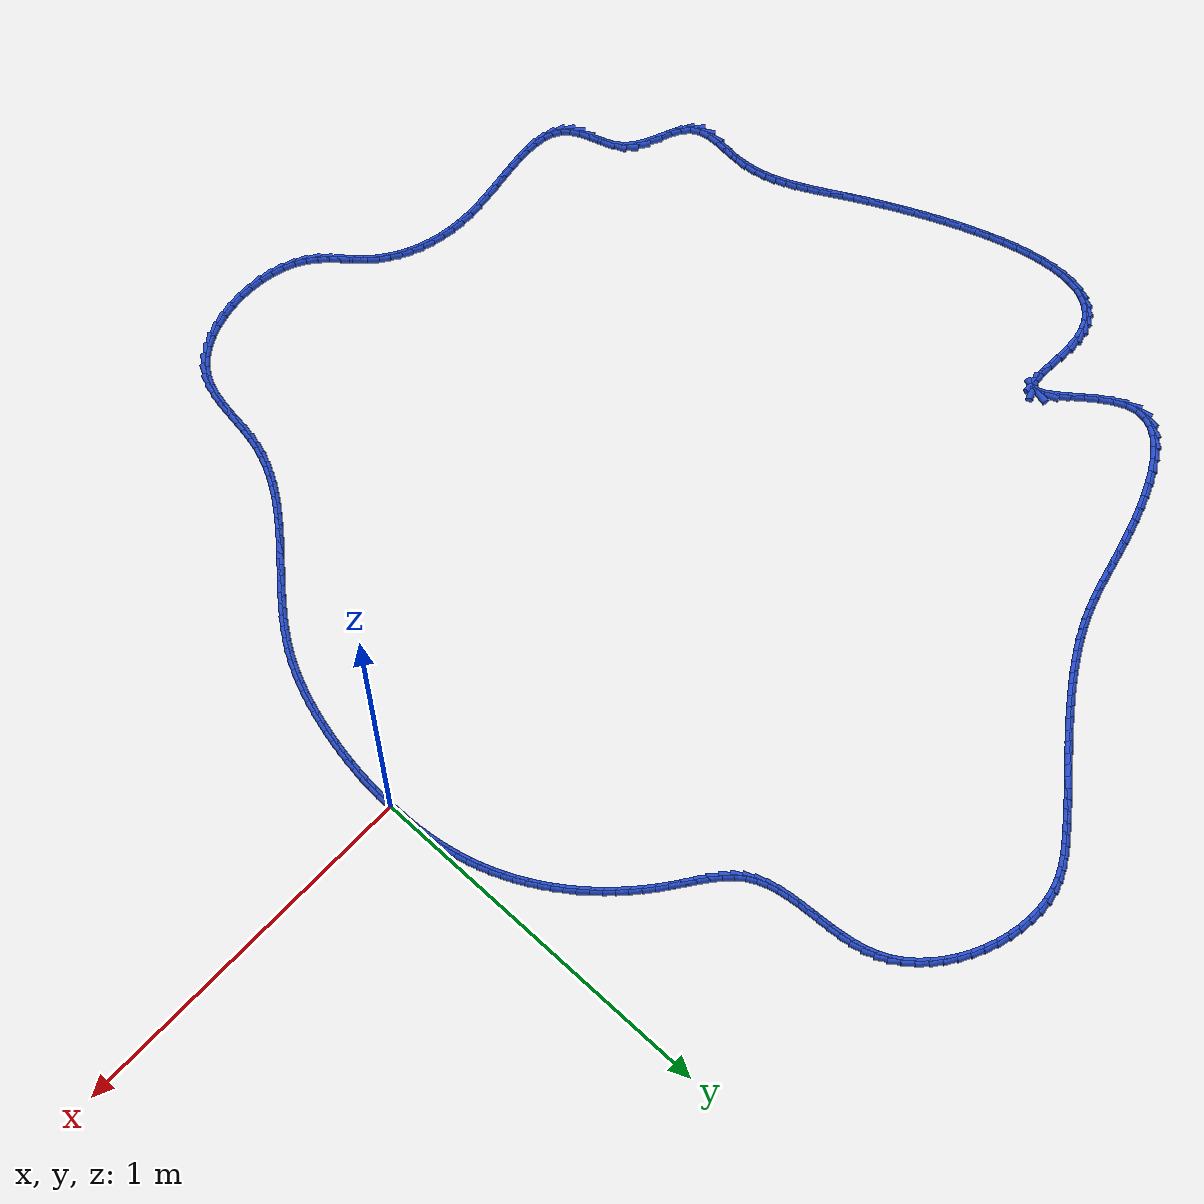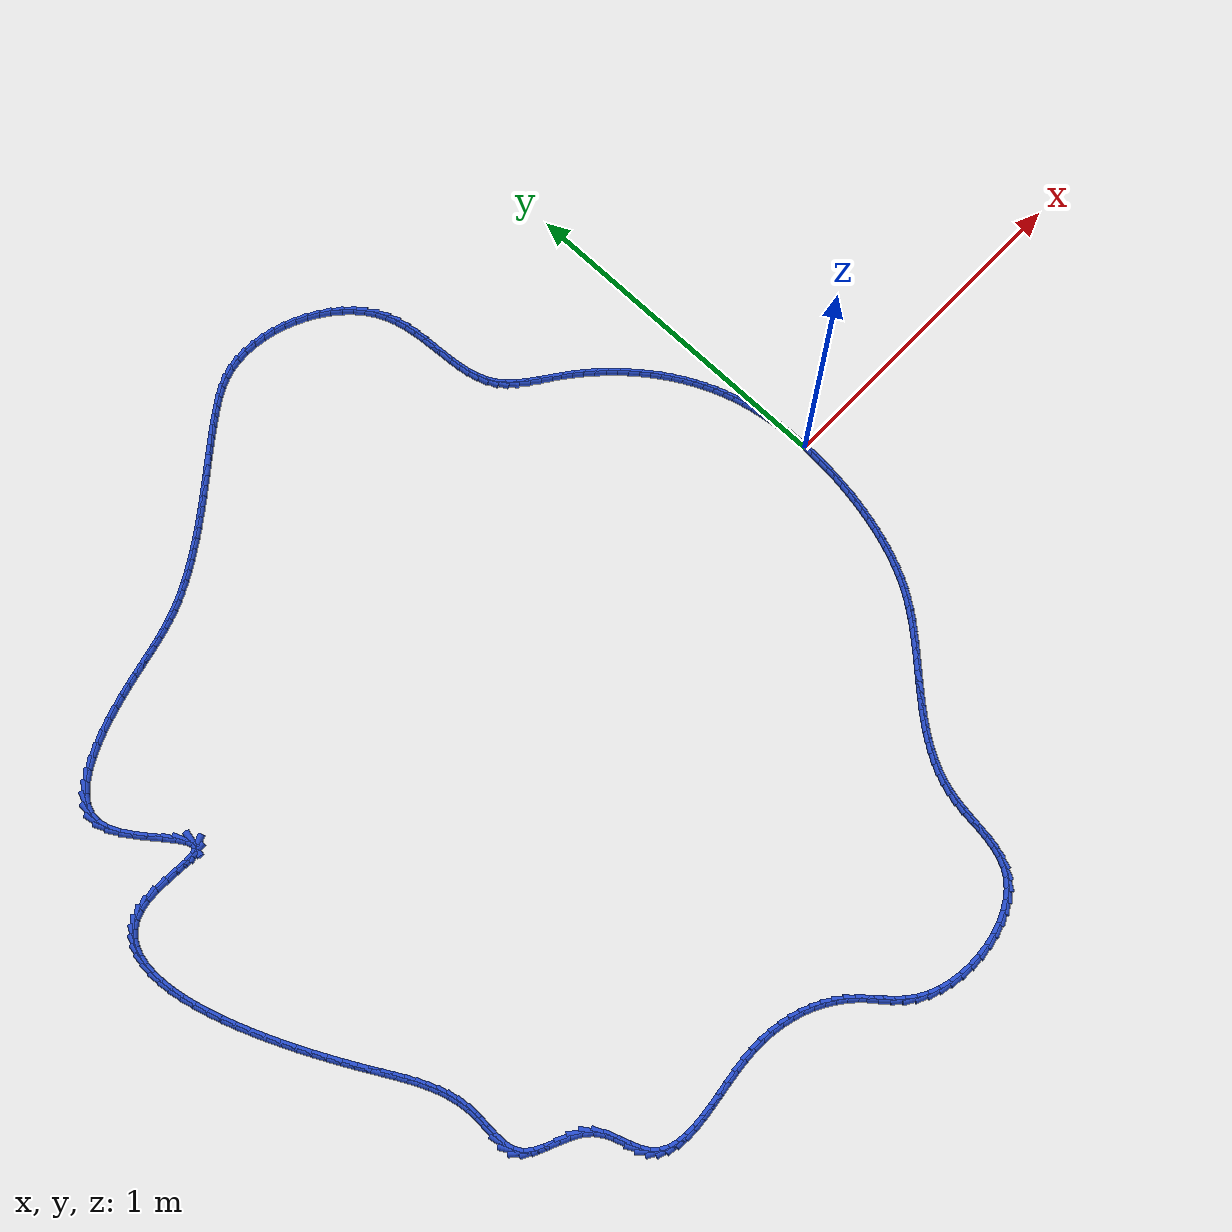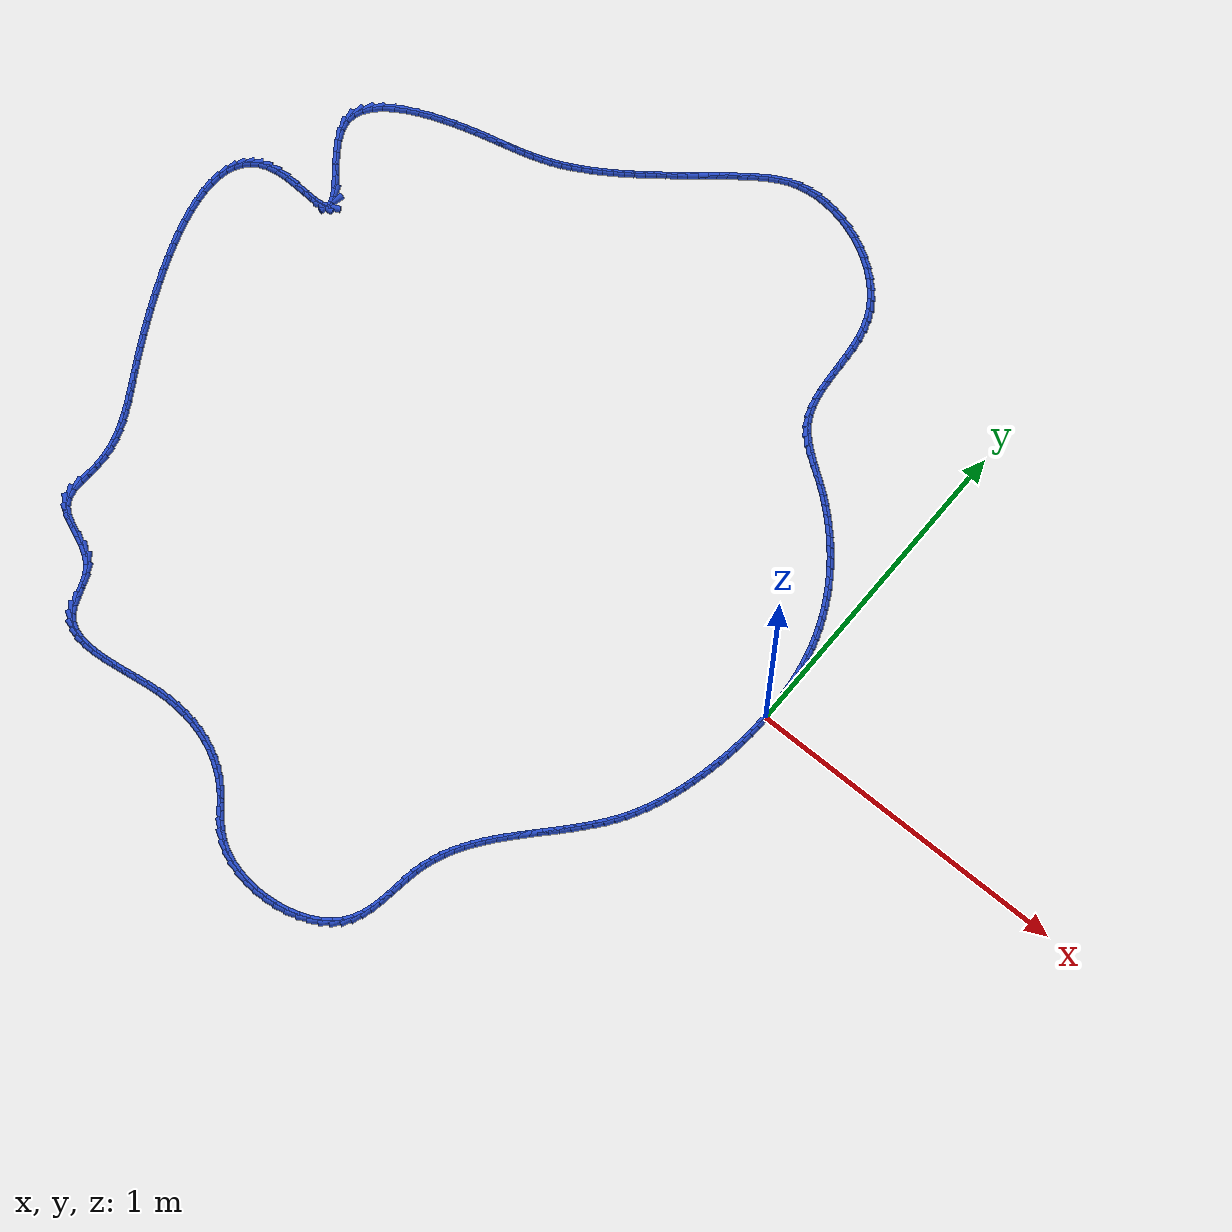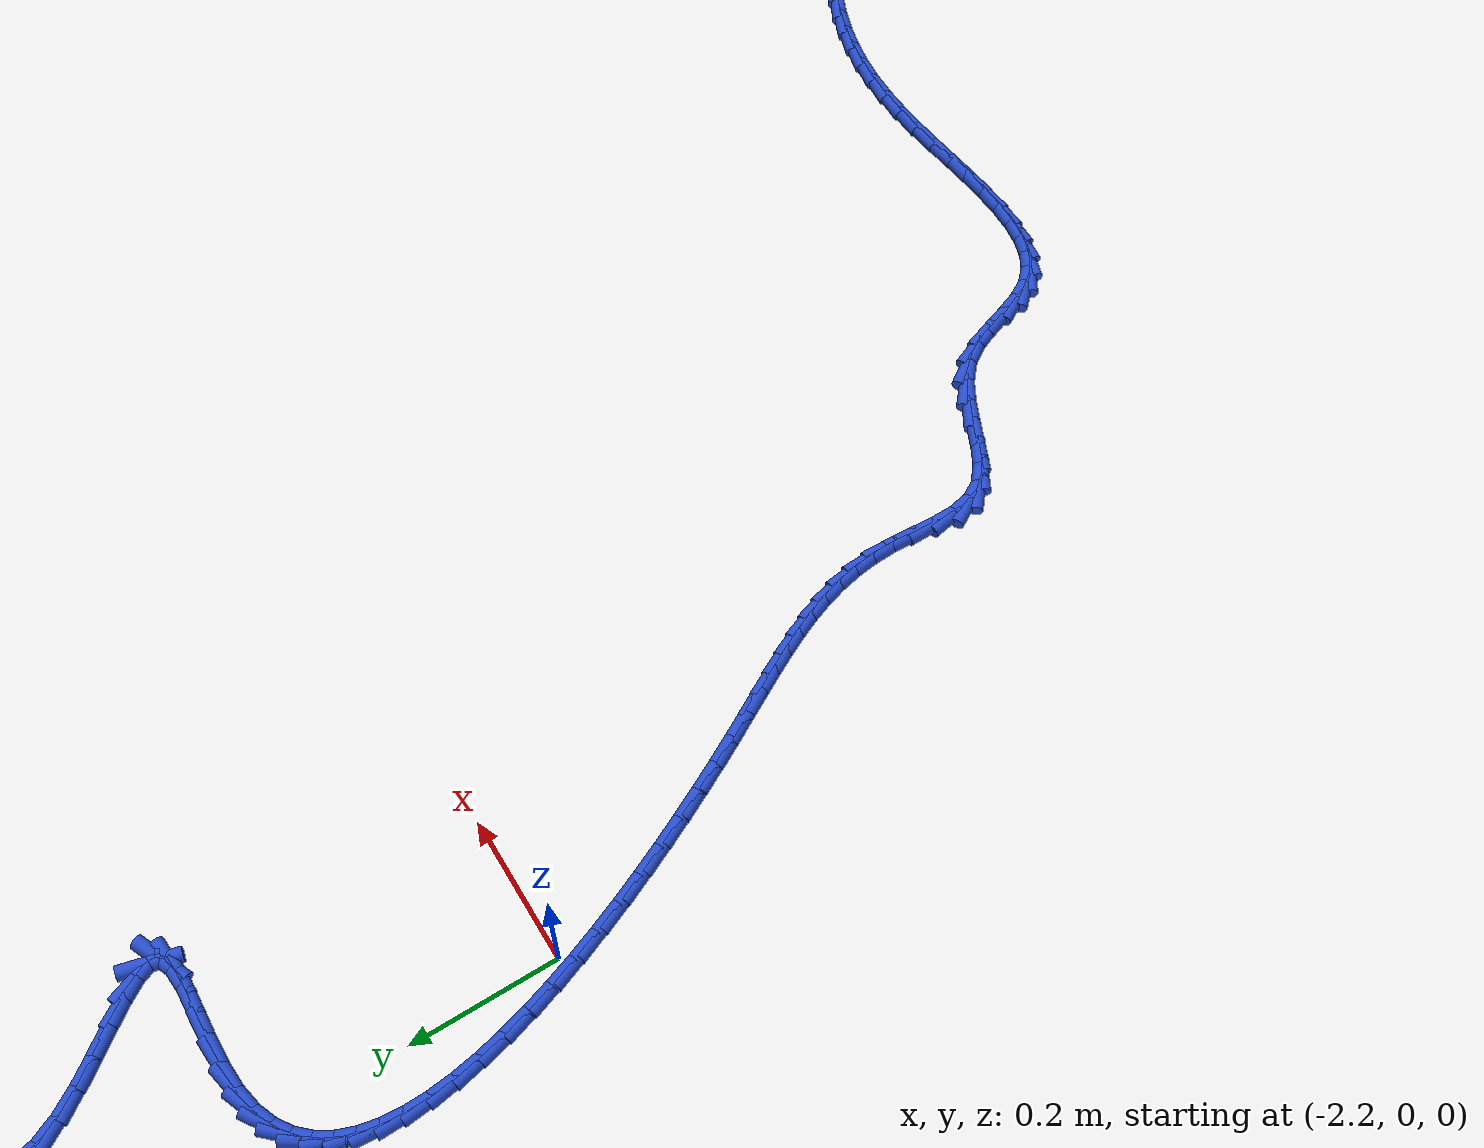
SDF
<sdf version="1.6">
 <world name="default">
  <light name="sun" type="directional">
   <pose>0 0 10 0 -0 0</pose>
   <diffuse>0.8 0.8 0.8 1</diffuse>
   <specular>0.2 0.2 0.2 1</specular>
   <attenuation>
    <range>1000</range>
    <constant>0.9</constant>
    <linear>0.01</linear>
    <quadratic>0.001</quadratic>
   </attenuation>
   <direction>-0.5 0.1 -0.9</direction>
  </light>
  <model name="ground_plane">
   <static>1</static>
   <link name="link">
    <collision name="collision">
     <geometry><plane><normal>0 0 1</normal><size>100 100</size></plane></geometry>
     <surface><friction><ode><mu>100</mu><mu2>50</mu2></ode></friction></surface>
    </collision>
    <visual name="visual">
     <cast_shadows>0</cast_shadows>
     <geometry><plane><normal>0 0 1</normal><size>100 100</size></plane></geometry>
     <material>
      <script><uri>file://media/materials/scripts/gazebo.material</uri><name>Gazebo/WhiteGlow</name></script>
     </material>
    </visual>
   </link>
  </model>
  <gravity>0 0 -9.8</gravity>
  <magnetic_field>6e-06 2.3e-05 -4.2e-05</magnetic_field>
  <atmosphere type="adiabatic"/>
  <physics name="default_physics" default="0" type="ode">
   <max_step_size>0.001</max_step_size>
   <real_time_factor>1</real_time_factor>
   <real_time_update_rate>1000</real_time_update_rate>
  </physics>
  <scene><ambient>0.4 0.4 0.4 1</ambient><background>0.7 0.7 0.7 1</background><shadows>1</shadows></scene>
  <spherical_coordinates>
   <surface_model>EARTH_WGS84</surface_model>
   <latitude_deg>0</latitude_deg>
   <longitude_deg>0</longitude_deg>
   <elevation>0</elevation>
   <heading_deg>0</heading_deg>
  </spherical_coordinates>
  <model name="line">
   <link name="link_0">
    <pose>3.903127820947816e-18 0.0 0.01 0 1.57 -1.5688685416763228</pose>
    <collision name="collision">
     <geometry><cylinder><radius>0.01</radius><length>0.08</length></cylinder></geometry>
    </collision>
    <visual name="visual">
     <material>
      <script><name>Gazebo/Blue</name><uri>file://media/materials/scripts/gazebo.material</uri></script>
     </material>
     <geometry><cylinder><radius>0.01</radius><length>0.08</length></cylinder></geometry>
    </visual>
   </link>
   <link name="link_1">
    <pose>-5.944774072849972e-05 0.030837289131833163 0.01 0 1.57 -1.538648523186415</pose>
    <collision name="collision">
     <geometry><cylinder><radius>0.01</radius><length>0.08</length></cylinder></geometry>
    </collision>
    <visual name="visual">
     <material>
      <script><name>Gazebo/Blue</name><uri>file://media/materials/scripts/gazebo.material</uri></script>
     </material>
     <geometry><cylinder><radius>0.01</radius><length>0.08</length></cylinder></geometry>
    </visual>
   </link>
   <link name="link_2">
    <pose>-0.0010516052413795341 0.061689029335046615 0.01 0 1.57 -1.5064721320048367</pose>
    <collision name="collision">
     <geometry><cylinder><radius>0.01</radius><length>0.08</length></cylinder></geometry>
    </collision>
    <visual name="visual">
     <material>
      <script><name>Gazebo/Blue</name><uri>file://media/materials/scripts/gazebo.material</uri></script>
     </material>
     <geometry><cylinder><radius>0.01</radius><length>0.08</length></cylinder></geometry>
    </visual>
   </link>
   <link name="link_3">
    <pose>-0.0030357017874402554 0.09249173631178999 0.01 0 1.57 -1.472216735551028</pose>
    <collision name="collision">
     <geometry><cylinder><radius>0.01</radius><length>0.08</length></cylinder></geometry>
    </collision>
    <visual name="visual">
     <material>
      <script><name>Gazebo/Blue</name><uri>file://media/materials/scripts/gazebo.material</uri></script>
     </material>
     <geometry><cylinder><radius>0.01</radius><length>0.08</length></cylinder></geometry>
    </visual>
   </link>
   <link name="link_4">
    <pose>-0.006070966664397824 0.12318192576421297 0.01 0 1.57 -1.4357629286368352</pose>
    <collision name="collision">
     <geometry><cylinder><radius>0.01</radius><length>0.08</length></cylinder></geometry>
    </collision>
    <visual name="visual">
     <material>
      <script><name>Gazebo/Blue</name><uri>file://media/materials/scripts/gazebo.material</uri></script>
     </material>
     <geometry><cylinder><radius>0.01</radius><length>0.08</length></cylinder></geometry>
    </visual>
   </link>
   <link name="link_5">
    <pose>-0.010216629157739396 0.15369611339446512 0.01 0 1.57 -1.3969989315505809</pose>
    <collision name="collision">
     <geometry><cylinder><radius>0.01</radius><length>0.08</length></cylinder></geometry>
    </collision>
    <visual name="visual">
     <material>
      <script><name>Gazebo/Blue</name><uri>file://media/materials/scripts/gazebo.material</uri></script>
     </material>
     <geometry><cylinder><radius>0.01</radius><length>0.08</length></cylinder></geometry>
    </visual>
   </link>
   <link name="link_6">
    <pose>-0.015531918552952124 0.1839708149046961 0.01 0 1.57 -1.3558261853358378</pose>
    <collision name="collision">
     <geometry><cylinder><radius>0.01</radius><length>0.08</length></cylinder></geometry>
    </collision>
    <visual name="visual">
     <material>
      <script><name>Gazebo/Blue</name><uri>file://media/materials/scripts/gazebo.material</uri></script>
     </material>
     <geometry><cylinder><radius>0.01</radius><length>0.08</length></cylinder></geometry>
    </visual>
   </link>
   <link name="link_7">
    <pose>-0.022076064135523172 0.2139425459970556 0.01 0 1.57 -1.3121662163758536</pose>
    <collision name="collision">
     <geometry><cylinder><radius>0.01</radius><length>0.08</length></cylinder></geometry>
    </collision>
    <visual name="visual">
     <material>
      <script><name>Gazebo/Blue</name><uri>file://media/materials/scripts/gazebo.material</uri></script>
     </material>
     <geometry><cylinder><radius>0.01</radius><length>0.08</length></cylinder></geometry>
    </visual>
   </link>
   <link name="link_8">
    <pose>-0.02990829519093969 0.24354782237369313 0.01 0 1.57 -1.2662745034594183</pose>
    <collision name="collision">
     <geometry><cylinder><radius>0.01</radius><length>0.08</length></cylinder></geometry>
    </collision>
    <visual name="visual">
     <material>
      <script><name>Gazebo/Blue</name><uri>file://media/materials/scripts/gazebo.material</uri></script>
     </material>
     <geometry><cylinder><radius>0.01</radius><length>0.08</length></cylinder></geometry>
    </visual>
   </link>
   <link name="link_9">
    <pose>-0.039079155079875694 0.27272671507767576 0.01 0 1.57 -1.220235402214348</pose>
    <collision name="collision">
     <geometry><cylinder><radius>0.01</radius><length>0.08</length></cylinder></geometry>
    </collision>
    <visual name="visual">
     <material>
      <script><name>Gazebo/Blue</name><uri>file://media/materials/scripts/gazebo.material</uri></script>
     </material>
     <geometry><cylinder><radius>0.01</radius><length>0.08</length></cylinder></geometry>
    </visual>
   </link>
   <link name="link_10">
    <pose>-0.0495798832912456 0.30144356953693513 0.01 0 1.57 -1.1749538954135756</pose>
    <collision name="collision">
     <geometry><cylinder><radius>0.01</radius><length>0.08</length></cylinder></geometry>
    </collision>
    <visual name="visual">
     <material>
      <script><name>Gazebo/Blue</name><uri>file://media/materials/scripts/gazebo.material</uri></script>
     </material>
     <geometry><cylinder><radius>0.01</radius><length>0.08</length></cylinder></geometry>
    </visual>
   </link>
   <link name="link_11">
    <pose>-0.06137693907104492 0.3296728742802801 0.01 0 1.57 -1.130457455954913</pose>
    <collision name="collision">
     <geometry><cylinder><radius>0.01</radius><length>0.08</length></cylinder></geometry>
    </collision>
    <visual name="visual">
     <material>
      <script><name>Gazebo/Blue</name><uri>file://media/materials/scripts/gazebo.material</uri></script>
     </material>
     <geometry><cylinder><radius>0.01</radius><length>0.08</length></cylinder></geometry>
    </visual>
   </link>
   <link name="link_12">
    <pose>-0.07443669855390374 0.35738915185583764 0.01 0 1.57 -1.0867579508593552</pose>
    <collision name="collision">
     <geometry><cylinder><radius>0.01</radius><length>0.08</length></cylinder></geometry>
    </collision>
    <visual name="visual">
     <material>
      <script><name>Gazebo/Blue</name><uri>file://media/materials/scripts/gazebo.material</uri></script>
     </material>
     <geometry><cylinder><radius>0.01</radius><length>0.08</length></cylinder></geometry>
    </visual>
   </link>
   <link name="link_13">
    <pose>-0.08872553787445203 0.38456692481173443 0.01 0 1.57 -1.04385568588925</pose>
    <collision name="collision">
     <geometry><cylinder><radius>0.01</radius><length>0.08</length></cylinder></geometry>
    </collision>
    <visual name="visual">
     <material>
      <script><name>Gazebo/Blue</name><uri>file://media/materials/scripts/gazebo.material</uri></script>
     </material>
     <geometry><cylinder><radius>0.01</radius><length>0.08</length></cylinder></geometry>
    </visual>
   </link>
   <link name="link_14">
    <pose>-0.10420983316731983 0.4111807156960974 0.01 0 1.57 -1.0017406390713344</pose>
    <collision name="collision">
     <geometry><cylinder><radius>0.01</radius><length>0.08</length></cylinder></geometry>
    </collision>
    <visual name="visual">
     <material>
      <script><name>Gazebo/Blue</name><uri>file://media/materials/scripts/gazebo.material</uri></script>
     </material>
     <geometry><cylinder><radius>0.01</radius><length>0.08</length></cylinder></geometry>
    </visual>
   </link>
   <link name="link_15">
    <pose>-0.12085596056713714 0.43720504705705326 0.01 0 1.57 -0.9603937432757044</pose>
    <collision name="collision">
     <geometry><cylinder><radius>0.01</radius><length>0.08</length></cylinder></geometry>
    </collision>
    <visual name="visual">
     <material>
      <script><name>Gazebo/Blue</name><uri>file://media/materials/scripts/gazebo.material</uri></script>
     </material>
     <geometry><cylinder><radius>0.01</radius><length>0.08</length></cylinder></geometry>
    </visual>
   </link>
   <link name="link_16">
    <pose>-0.13863029620853415 0.4626144414427294 0.01 0 1.57 -0.9197881642914152</pose>
    <collision name="collision">
     <geometry><cylinder><radius>0.01</radius><length>0.08</length></cylinder></geometry>
    </collision>
    <visual name="visual">
     <material>
      <script><name>Gazebo/Blue</name><uri>file://media/materials/scripts/gazebo.material</uri></script>
     </material>
     <geometry><cylinder><radius>0.01</radius><length>0.08</length></cylinder></geometry>
    </visual>
   </link>
   <link name="link_17">
    <pose>-0.15749921622614063 0.4873834214012518 0.01 0 1.57 -0.8798905333932457</pose>
    <collision name="collision">
     <geometry><cylinder><radius>0.01</radius><length>0.08</length></cylinder></geometry>
    </collision>
    <visual name="visual">
     <material>
      <script><name>Gazebo/Blue</name><uri>file://media/materials/scripts/gazebo.material</uri></script>
     </material>
     <geometry><cylinder><radius>0.01</radius><length>0.08</length></cylinder></geometry>
    </visual>
   </link>
   <link name="link_18">
    <pose>-0.17742909675458682 0.511486509480748 0.01 0 1.57 -0.8406621053352632</pose>
    <collision name="collision">
     <geometry><cylinder><radius>0.01</radius><length>0.08</length></cylinder></geometry>
    </collision>
    <visual name="visual">
     <material>
      <script><name>Gazebo/Blue</name><uri>file://media/materials/scripts/gazebo.material</uri></script>
     </material>
     <geometry><cylinder><radius>0.01</radius><length>0.08</length></cylinder></geometry>
    </visual>
   </link>
   <link name="link_19">
    <pose>-0.19838631392850253 0.5348982282293444 0.01 0 1.57 -0.8020598233163297</pose>
    <collision name="collision">
     <geometry><cylinder><radius>0.01</radius><length>0.08</length></cylinder></geometry>
    </collision>
    <visual name="visual">
     <material>
      <script><name>Gazebo/Blue</name><uri>file://media/materials/scripts/gazebo.material</uri></script>
     </material>
     <geometry><cylinder><radius>0.01</radius><length>0.08</length></cylinder></geometry>
    </visual>
   </link>
   <link name="link_20">
    <pose>-0.22033724388251802 0.5575931001951681 0.01 0 1.57 -0.7640372813641009</pose>
    <collision name="collision">
     <geometry><cylinder><radius>0.01</radius><length>0.08</length></cylinder></geometry>
    </collision>
    <visual name="visual">
     <material>
      <script><name>Gazebo/Blue</name><uri>file://media/materials/scripts/gazebo.material</uri></script>
     </material>
     <geometry><cylinder><radius>0.01</radius><length>0.08</length></cylinder></geometry>
    </visual>
   </link>
   <link name="link_21">
    <pose>-0.2432482627512632 0.5795456479263459 0.01 0 1.57 -0.7265455816710567</pose>
    <collision name="collision">
     <geometry><cylinder><radius>0.01</radius><length>0.08</length></cylinder></geometry>
    </collision>
    <visual name="visual">
     <material>
      <script><name>Gazebo/Blue</name><uri>file://media/materials/scripts/gazebo.material</uri></script>
     </material>
     <geometry><cylinder><radius>0.01</radius><length>0.08</length></cylinder></geometry>
    </visual>
   </link>
   <link name="link_22">
    <pose>-0.267085746669368 0.6007303939710045 0.01 0 1.57 -0.689534089764673</pose>
    <collision name="collision">
     <geometry><cylinder><radius>0.01</radius><length>0.08</length></cylinder></geometry>
    </collision>
    <visual name="visual">
     <material>
      <script><name>Gazebo/Blue</name><uri>file://media/materials/scripts/gazebo.material</uri></script>
     </material>
     <geometry><cylinder><radius>0.01</radius><length>0.08</length></cylinder></geometry>
    </visual>
   </link>
   <link name="link_23">
    <pose>-0.2918160717714628 0.6211218608772711 0.01 0 1.57 -0.6529570581898443</pose>
    <collision name="collision">
     <geometry><cylinder><radius>0.01</radius><length>0.08</length></cylinder></geometry>
    </collision>
    <visual name="visual">
     <material>
      <script><name>Gazebo/Blue</name><uri>file://media/materials/scripts/gazebo.material</uri></script>
     </material>
     <geometry><cylinder><radius>0.01</radius><length>0.08</length></cylinder></geometry>
    </visual>
   </link>
   <link name="link_24">
    <pose>-0.3174054466141527 0.6406946849177441 0.01 0 1.57 -0.6231023706121911</pose>
    <collision name="collision">
     <geometry><cylinder><radius>0.01</radius><length>0.08</length></cylinder></geometry>
    </collision>
    <visual name="visual">
     <material>
      <script><name>Gazebo/Blue</name><uri>file://media/materials/scripts/gazebo.material</uri></script>
     </material>
     <geometry><cylinder><radius>0.01</radius><length>0.08</length></cylinder></geometry>
    </visual>
   </link>
   <link name="link_25">
    <pose>-0.34363913993469325 0.6595462946312632 0.01 0 1.57 -0.6180805681650074</pose>
    <collision name="collision">
     <geometry><cylinder><radius>0.01</radius><length>0.08</length></cylinder></geometry>
    </collision>
    <visual name="visual">
     <material>
      <script><name>Gazebo/Blue</name><uri>file://media/materials/scripts/gazebo.material</uri></script>
     </material>
     <geometry><cylinder><radius>0.01</radius><length>0.08</length></cylinder></geometry>
    </visual>
   </link>
   <link name="link_26">
    <pose>-0.3697769824308998 0.6781306996998544 0.01 0 1.57 -0.641730024394646</pose>
    <collision name="collision">
     <geometry><cylinder><radius>0.01</radius><length>0.08</length></cylinder></geometry>
    </collision>
    <visual name="visual">
     <material>
      <script><name>Gazebo/Blue</name><uri>file://media/materials/scripts/gazebo.material</uri></script>
     </material>
     <geometry><cylinder><radius>0.01</radius><length>0.08</length></cylinder></geometry>
    </visual>
   </link>
   <link name="link_27">
    <pose>-0.3949839637280703 0.696966272366914 0.01 0 1.57 -0.6965194888791109</pose>
    <collision name="collision">
     <geometry><cylinder><radius>0.01</radius><length>0.08</length></cylinder></geometry>
    </collision>
    <visual name="visual">
     <material>
      <script><name>Gazebo/Blue</name><uri>file://media/materials/scripts/gazebo.material</uri></script>
     </material>
     <geometry><cylinder><radius>0.01</radius><length>0.08</length></cylinder></geometry>
    </visual>
   </link>
   <link name="link_28">
    <pose>-0.41842507345150276 0.7165713848758379 0.01 0 1.57 -0.7866632646782865</pose>
    <collision name="collision">
     <geometry><cylinder><radius>0.01</radius><length>0.08</length></cylinder></geometry>
    </collision>
    <visual name="visual">
     <material>
      <script><name>Gazebo/Blue</name><uri>file://media/materials/scripts/gazebo.material</uri></script>
     </material>
     <geometry><cylinder><radius>0.01</radius><length>0.08</length></cylinder></geometry>
    </visual>
   </link>
   <link name="link_29">
    <pose>-0.4392653012264947 0.7374644094700225 0.01 0 1.57 -0.9166633043658768</pose>
    <collision name="collision">
     <geometry><cylinder><radius>0.01</radius><length>0.08</length></cylinder></geometry>
    </collision>
    <visual name="visual">
     <material>
      <script><name>Gazebo/Blue</name><uri>file://media/materials/scripts/gazebo.material</uri></script>
     </material>
     <geometry><cylinder><radius>0.01</radius><length>0.08</length></cylinder></geometry>
    </visual>
   </link>
   <link name="link_30">
    <pose>-0.45666983380540066 0.7601636090838435 0.01 0 1.57 -1.0745274896062629</pose>
    <collision name="collision">
     <geometry><cylinder><radius>0.01</radius><length>0.08</length></cylinder></geometry>
    </collision>
    <visual name="visual">
     <material>
      <script><name>Gazebo/Blue</name><uri>file://media/materials/scripts/gazebo.material</uri></script>
     </material>
     <geometry><cylinder><radius>0.01</radius><length>0.08</length></cylinder></geometry>
    </visual>
   </link>
   <link name="link_31">
    <pose>-0.4701233851103939 0.7850100654852579 0.01 0 1.57 -1.2150561311433625</pose>
    <collision name="collision">
     <geometry><cylinder><radius>0.01</radius><length>0.08</length></cylinder></geometry>
    </collision>
    <visual name="visual">
     <material>
      <script><name>Gazebo/Blue</name><uri>file://media/materials/scripts/gazebo.material</uri></script>
     </material>
     <geometry><cylinder><radius>0.01</radius><length>0.08</length></cylinder></geometry>
    </visual>
   </link>
   <link name="link_32">
    <pose>-0.4800798719454025 0.8118074272806429 0.01 0 1.57 -1.3263532260639526</pose>
    <collision name="collision">
     <geometry><cylinder><radius>0.01</radius><length>0.08</length></cylinder></geometry>
    </collision>
    <visual name="visual">
     <material>
      <script><name>Gazebo/Blue</name><uri>file://media/materials/scripts/gazebo.material</uri></script>
     </material>
     <geometry><cylinder><radius>0.01</radius><length>0.08</length></cylinder></geometry>
    </visual>
   </link>
   <link name="link_33">
    <pose>-0.4871762847262714 0.8402578268387492 0.01 0 1.57 -1.4087264314905321</pose>
    <collision name="collision">
     <geometry><cylinder><radius>0.01</radius><length>0.08</length></cylinder></geometry>
    </collision>
    <visual name="visual">
     <material>
      <script><name>Gazebo/Blue</name><uri>file://media/materials/scripts/gazebo.material</uri></script>
     </material>
     <geometry><cylinder><radius>0.01</radius><length>0.08</length></cylinder></geometry>
    </visual>
   </link>
   <link name="link_34">
    <pose>-0.4920496138688452 0.8700633965283256 0.01 0 1.57 -1.464685364569837</pose>
    <collision name="collision">
     <geometry><cylinder><radius>0.01</radius><length>0.08</length></cylinder></geometry>
    </collision>
    <visual name="visual">
     <material>
      <script><name>Gazebo/Blue</name><uri>file://media/materials/scripts/gazebo.material</uri></script>
     </material>
     <geometry><cylinder><radius>0.01</radius><length>0.08</length></cylinder></geometry>
    </visual>
   </link>
   <link name="link_35">
    <pose>-0.4953368497889686 0.9009262687181222 0.01 0 1.57 -1.4969912704122534</pose>
    <collision name="collision">
     <geometry><cylinder><radius>0.01</radius><length>0.08</length></cylinder></geometry>
    </collision>
    <visual name="visual">
     <material>
      <script><name>Gazebo/Blue</name><uri>file://media/materials/scripts/gazebo.material</uri></script>
     </material>
     <geometry><cylinder><radius>0.01</radius><length>0.08</length></cylinder></geometry>
    </visual>
   </link>
   <link name="link_36">
    <pose>-0.4976749829024867 0.9325485757768893 0.01 0 1.57 -1.5077324297632582</pose>
    <collision name="collision">
     <geometry><cylinder><radius>0.01</radius><length>0.08</length></cylinder></geometry>
    </collision>
    <visual name="visual">
     <material>
      <script><name>Gazebo/Blue</name><uri>file://media/materials/scripts/gazebo.material</uri></script>
     </material>
     <geometry><cylinder><radius>0.01</radius><length>0.08</length></cylinder></geometry>
    </visual>
   </link>
   <link name="link_37">
    <pose>-0.49970100362524383 0.9646324500733761 0.01 0 1.57 -1.4980234955988367</pose>
    <collision name="collision">
     <geometry><cylinder><radius>0.01</radius><length>0.08</length></cylinder></geometry>
    </collision>
    <visual name="visual">
     <material>
      <script><name>Gazebo/Blue</name><uri>file://media/materials/scripts/gazebo.material</uri></script>
     </material>
     <geometry><cylinder><radius>0.01</radius><length>0.08</length></cylinder></geometry>
    </visual>
   </link>
   <link name="link_38">
    <pose>-0.5020519023730848 0.9968800239763324 0.01 0 1.57 -1.4680015450760784</pose>
    <collision name="collision">
     <geometry><cylinder><radius>0.01</radius><length>0.08</length></cylinder></geometry>
    </collision>
    <visual name="visual">
     <material>
      <script><name>Gazebo/Blue</name><uri>file://media/materials/scripts/gazebo.material</uri></script>
     </material>
     <geometry><cylinder><radius>0.01</radius><length>0.08</length></cylinder></geometry>
    </visual>
   </link>
   <link name="link_39">
    <pose>-0.5053646695618547 1.028993429854508 0.01 0 1.57 -1.416988781989304</pose>
    <collision name="collision">
     <geometry><cylinder><radius>0.01</radius><length>0.08</length></cylinder></geometry>
    </collision>
    <visual name="visual">
     <material>
      <script><name>Gazebo/Blue</name><uri>file://media/materials/scripts/gazebo.material</uri></script>
     </material>
     <geometry><cylinder><radius>0.01</radius><length>0.08</length></cylinder></geometry>
    </visual>
   </link>
   <link name="link_40">
    <pose>-0.510276295607398 1.060674800076653 0.01 0 1.57 -1.3438493507840725</pose>
    <collision name="collision">
     <geometry><cylinder><radius>0.01</radius><length>0.08</length></cylinder></geometry>
    </collision>
    <visual name="visual">
     <material>
      <script><name>Gazebo/Blue</name><uri>file://media/materials/scripts/gazebo.material</uri></script>
     </material>
     <geometry><cylinder><radius>0.01</radius><length>0.08</length></cylinder></geometry>
    </visual>
   </link>
   <link name="link_41">
    <pose>-0.5174237709255591 1.0916262670115167 0.01 0 1.57 -1.2476704142732296</pose>
    <collision name="collision">
     <geometry><cylinder><radius>0.01</radius><length>0.08</length></cylinder></geometry>
    </collision>
    <visual name="visual">
     <material>
      <script><name>Gazebo/Blue</name><uri>file://media/materials/scripts/gazebo.material</uri></script>
     </material>
     <geometry><cylinder><radius>0.01</radius><length>0.08</length></cylinder></geometry>
    </visual>
   </link>
   <link name="link_42">
    <pose>-0.5274440859321834 1.1215499630278487 0.01 0 1.57 -1.1298664862024286</pose>
    <collision name="collision">
     <geometry><cylinder><radius>0.01</radius><length>0.08</length></cylinder></geometry>
    </collision>
    <visual name="visual">
     <material>
      <script><name>Gazebo/Blue</name><uri>file://media/materials/scripts/gazebo.material</uri></script>
     </material>
     <geometry><cylinder><radius>0.01</radius><length>0.08</length></cylinder></geometry>
    </visual>
   </link>
   <link name="link_43">
    <pose>-0.5409423319355913 1.1501529746308705 0.01 0 1.57 -1.0085178067597893</pose>
    <collision name="collision">
     <geometry><cylinder><radius>0.01</radius><length>0.08</length></cylinder></geometry>
    </collision>
    <visual name="visual">
     <material>
      <script><name>Gazebo/Blue</name><uri>file://media/materials/scripts/gazebo.material</uri></script>
     </material>
     <geometry><cylinder><radius>0.01</radius><length>0.08</length></cylinder></geometry>
    </visual>
   </link>
   <link name="link_44">
    <pose>-0.5580003314924393 1.1772236553269166 0.01 0 1.57 -0.897079715083553</pose>
    <collision name="collision">
     <geometry><cylinder><radius>0.01</radius><length>0.08</length></cylinder></geometry>
    </collision>
    <visual name="visual">
     <material>
      <script><name>Gazebo/Blue</name><uri>file://media/materials/scripts/gazebo.material</uri></script>
     </material>
     <geometry><cylinder><radius>0.01</radius><length>0.08</length></cylinder></geometry>
    </visual>
   </link>
   <link name="link_45">
    <pose>-0.5782722103292995 1.2026167826896061 0.01 0 1.57 -0.7949259154296981</pose>
    <collision name="collision">
     <geometry><cylinder><radius>0.01</radius><length>0.08</length></cylinder></geometry>
    </collision>
    <visual name="visual">
     <material>
      <script><name>Gazebo/Blue</name><uri>file://media/materials/scripts/gazebo.material</uri></script>
     </material>
     <geometry><cylinder><radius>0.01</radius><length>0.08</length></cylinder></geometry>
    </visual>
   </link>
   <link name="link_46">
    <pose>-0.6013995535018942 1.2261890819393602 0.01 0 1.57 -0.700572011375388</pose>
    <collision name="collision">
     <geometry><cylinder><radius>0.01</radius><length>0.08</length></cylinder></geometry>
    </collision>
    <visual name="visual">
     <material>
      <script><name>Gazebo/Blue</name><uri>file://media/materials/scripts/gazebo.material</uri></script>
     </material>
     <geometry><cylinder><radius>0.01</radius><length>0.08</length></cylinder></geometry>
    </visual>
   </link>
   <link name="link_47">
    <pose>-0.6270239460659456 1.2477972782966018 0.01 0 1.57 -0.6123365396463943</pose>
    <collision name="collision">
     <geometry><cylinder><radius>0.01</radius><length>0.08</length></cylinder></geometry>
    </collision>
    <visual name="visual">
     <material>
      <script><name>Gazebo/Blue</name><uri>file://media/materials/scripts/gazebo.material</uri></script>
     </material>
     <geometry><cylinder><radius>0.01</radius><length>0.08</length></cylinder></geometry>
    </visual>
   </link>
   <link name="link_48">
    <pose>-0.654786973077176 1.2672980969817524 0.01 0 1.57 -0.5284937240804494</pose>
    <collision name="collision">
     <geometry><cylinder><radius>0.01</radius><length>0.08</length></cylinder></geometry>
    </collision>
    <visual name="visual">
     <material>
      <script><name>Gazebo/Blue</name><uri>file://media/materials/scripts/gazebo.material</uri></script>
     </material>
     <geometry><cylinder><radius>0.01</radius><length>0.08</length></cylinder></geometry>
    </visual>
   </link>
   <link name="link_49">
    <pose>-0.6843302195913078 1.2845482632152347 0.01 0 1.57 -0.44733660933894726</pose>
    <collision name="collision">
     <geometry><cylinder><radius>0.01</radius><length>0.08</length></cylinder></geometry>
    </collision>
    <visual name="visual">
     <material>
      <script><name>Gazebo/Blue</name><uri>file://media/materials/scripts/gazebo.material</uri></script>
     </material>
     <geometry><cylinder><radius>0.01</radius><length>0.08</length></cylinder></geometry>
    </visual>
   </link>
   <link name="link_50">
    <pose>-0.7152952706640631 1.299404502217471 0.01 0 1.57 -0.3671848753250154</pose>
    <collision name="collision">
     <geometry><cylinder><radius>0.01</radius><length>0.08</length></cylinder></geometry>
    </collision>
    <visual name="visual">
     <material>
      <script><name>Gazebo/Blue</name><uri>file://media/materials/scripts/gazebo.material</uri></script>
     </material>
     <geometry><cylinder><radius>0.01</radius><length>0.08</length></cylinder></geometry>
    </visual>
   </link>
   <link name="link_51">
    <pose>-0.7473237113511644 1.3117235392088826 0.01 0 1.57 -0.2863630984443288</pose>
    <collision name="collision">
     <geometry><cylinder><radius>0.01</radius><length>0.08</length></cylinder></geometry>
    </collision>
    <visual name="visual">
     <material>
      <script><name>Gazebo/Blue</name><uri>file://media/materials/scripts/gazebo.material</uri></script>
     </material>
     <geometry><cylinder><radius>0.01</radius><length>0.08</length></cylinder></geometry>
    </visual>
   </link>
   <link name="link_52">
    <pose>-0.7800571267083338 1.321362099409893 0.01 0 1.57 -0.2031677565558003</pose>
    <collision name="collision">
     <geometry><cylinder><radius>0.01</radius><length>0.08</length></cylinder></geometry>
    </collision>
    <visual name="visual">
     <material>
      <script><name>Gazebo/Blue</name><uri>file://media/materials/scripts/gazebo.material</uri></script>
     </material>
     <geometry><cylinder><radius>0.01</radius><length>0.08</length></cylinder></geometry>
    </visual>
   </link>
   <link name="link_53">
    <pose>-0.8131371017912935 1.3281769080409227 0.01 0 1.57 -0.11583834713216741</pose>
    <collision name="collision">
     <geometry><cylinder><radius>0.01</radius><length>0.08</length></cylinder></geometry>
    </collision>
    <visual name="visual">
     <material>
      <script><name>Gazebo/Blue</name><uri>file://media/materials/scripts/gazebo.material</uri></script>
     </material>
     <geometry><cylinder><radius>0.01</radius><length>0.08</length></cylinder></geometry>
    </visual>
   </link>
   <link name="link_54">
    <pose>-0.8462052216557658 1.3320246903223947 0.01 0 1.57 -0.022550600253544082</pose>
    <collision name="collision">
     <geometry><cylinder><radius>0.01</radius><length>0.08</length></cylinder></geometry>
    </collision>
    <visual name="visual">
     <material>
      <script><name>Gazebo/Blue</name><uri>file://media/materials/scripts/gazebo.material</uri></script>
     </material>
     <geometry><cylinder><radius>0.01</radius><length>0.08</length></cylinder></geometry>
    </visual>
   </link>
   <link name="link_55">
    <pose>-0.8789030713574737 1.3327621714747315 0.01 0 1.57 0.07854189724979344</pose>
    <collision name="collision">
     <geometry><cylinder><radius>0.01</radius><length>0.08</length></cylinder></geometry>
    </collision>
    <visual name="visual">
     <material>
      <script><name>Gazebo/Blue</name><uri>file://media/materials/scripts/gazebo.material</uri></script>
     </material>
     <geometry><cylinder><radius>0.01</radius><length>0.08</length></cylinder></geometry>
    </visual>
   </link>
   <link name="link_56">
    <pose>-0.9108722359521386 1.3302460767183546 0.01 0 1.57 0.18917898786006135</pose>
    <collision name="collision">
     <geometry><cylinder><radius>0.01</radius><length>0.08</length></cylinder></geometry>
    </collision>
    <visual name="visual">
     <material>
      <script><name>Gazebo/Blue</name><uri>file://media/materials/scripts/gazebo.material</uri></script>
     </material>
     <geometry><cylinder><radius>0.01</radius><length>0.08</length></cylinder></geometry>
    </visual>
   </link>
   <link name="link_57">
    <pose>-0.9417543004954834 1.3243331312736872 0.01 0 1.57 0.310371444108355</pose>
    <collision name="collision">
     <geometry><cylinder><radius>0.01</radius><length>0.08</length></cylinder></geometry>
    </collision>
    <visual name="visual">
     <material>
      <script><name>Gazebo/Blue</name><uri>file://media/materials/scripts/gazebo.material</uri></script>
     </material>
     <geometry><cylinder><radius>0.01</radius><length>0.08</length></cylinder></geometry>
    </visual>
   </link>
   <link name="link_58">
    <pose>-0.971197612150102 1.3148895685342872 0.01 0 1.57 0.42788248551583796</pose>
    <collision name="collision">
     <geometry><cylinder><radius>0.01</radius><length>0.08</length></cylinder></geometry>
    </collision>
    <visual name="visual">
     <material>
      <script><name>Gazebo/Blue</name><uri>file://media/materials/scripts/gazebo.material</uri></script>
     </material>
     <geometry><cylinder><radius>0.01</radius><length>0.08</length></cylinder></geometry>
    </visual>
   </link>
   <link name="link_59">
    <pose>-0.9991171688426635 1.3021565585340167 0.01 0 1.57 0.5207621515845853</pose>
    <collision name="collision">
     <geometry><cylinder><radius>0.01</radius><length>0.08</length></cylinder></geometry>
    </collision>
    <visual name="visual">
     <material>
      <script><name>Gazebo/Blue</name><uri>file://media/materials/scripts/gazebo.material</uri></script>
     </material>
     <geometry><cylinder><radius>0.01</radius><length>0.08</length></cylinder></geometry>
    </visual>
   </link>
   <link name="link_60">
    <pose>-1.0257765564623886 1.2868654195348226 0.01 0 1.57 0.586941643941539</pose>
    <collision name="collision">
     <geometry><cylinder><radius>0.01</radius><length>0.08</length></cylinder></geometry>
    </collision>
    <visual name="visual">
     <material>
      <script><name>Gazebo/Blue</name><uri>file://media/materials/scripts/gazebo.material</uri></script>
     </material>
     <geometry><cylinder><radius>0.01</radius><length>0.08</length></cylinder></geometry>
    </visual>
   </link>
   <link name="link_61">
    <pose>-1.0514628801616983 1.2697805401465179 0.01 0 1.57 0.6270198667300313</pose>
    <collision name="collision">
     <geometry><cylinder><radius>0.01</radius><length>0.08</length></cylinder></geometry>
    </collision>
    <visual name="visual">
     <material>
      <script><name>Gazebo/Blue</name><uri>file://media/materials/scripts/gazebo.material</uri></script>
     </material>
     <geometry><cylinder><radius>0.01</radius><length>0.08</length></cylinder></geometry>
    </visual>
   </link>
   <link name="link_62">
    <pose>-1.0764632357896622 1.2516662770911948 0.01 0 1.57 0.6461332044613861</pose>
    <collision name="collision">
     <geometry><cylinder><radius>0.01</radius><length>0.08</length></cylinder></geometry>
    </collision>
    <visual name="visual">
     <material>
      <script><name>Gazebo/Blue</name><uri>file://media/materials/scripts/gazebo.material</uri></script>
     </material>
     <geometry><cylinder><radius>0.01</radius><length>0.08</length></cylinder></geometry>
    </visual>
   </link>
   <link name="link_63">
    <pose>-1.1010233003190384 1.2331450217339932 0.01 0 1.57 0.6592204816249908</pose>
    <collision name="collision">
     <geometry><cylinder><radius>0.01</radius><length>0.08</length></cylinder></geometry>
    </collision>
    <visual name="visual">
     <material>
      <script><name>Gazebo/Blue</name><uri>file://media/materials/scripts/gazebo.material</uri></script>
     </material>
     <geometry><cylinder><radius>0.01</radius><length>0.08</length></cylinder></geometry>
    </visual>
   </link>
   <link name="link_64">
    <pose>-1.125252192341035 1.2143711044710437 0.01 0 1.57 0.6692647758033092</pose>
    <collision name="collision">
     <geometry><cylinder><radius>0.01</radius><length>0.08</length></cylinder></geometry>
    </collision>
    <visual name="visual">
     <material>
      <script><name>Gazebo/Blue</name><uri>file://media/materials/scripts/gazebo.material</uri></script>
     </material>
     <geometry><cylinder><radius>0.01</radius><length>0.08</length></cylinder></geometry>
    </visual>
   </link>
   <link name="link_65">
    <pose>-1.1492309271927637 1.1954025303305666 0.01 0 1.57 0.6762130828674482</pose>
    <collision name="collision">
     <geometry><cylinder><radius>0.01</radius><length>0.08</length></cylinder></geometry>
    </collision>
    <visual name="visual">
     <material>
      <script><name>Gazebo/Blue</name><uri>file://media/materials/scripts/gazebo.material</uri></script>
     </material>
     <geometry><cylinder><radius>0.01</radius><length>0.08</length></cylinder></geometry>
    </visual>
   </link>
   <link name="link_66">
    <pose>-1.1730405202113368 1.1762973043407834 0.01 0 1.57 0.6800315810141967</pose>
    <collision name="collision">
     <geometry><cylinder><radius>0.01</radius><length>0.08</length></cylinder></geometry>
    </collision>
    <visual name="visual">
     <material>
      <script><name>Gazebo/Blue</name><uri>file://media/materials/scripts/gazebo.material</uri></script>
     </material>
     <geometry><cylinder><radius>0.01</radius><length>0.08</length></cylinder></geometry>
    </visual>
   </link>
   <link name="link_67">
    <pose>-1.1967619867338675 1.1571134315299154 0.01 0 1.57 0.6807040863771685</pose>
    <collision name="collision">
     <geometry><cylinder><radius>0.01</radius><length>0.08</length></cylinder></geometry>
    </collision>
    <visual name="visual">
     <material>
      <script><name>Gazebo/Blue</name><uri>file://media/materials/scripts/gazebo.material</uri></script>
     </material>
     <geometry><cylinder><radius>0.01</radius><length>0.08</length></cylinder></geometry>
    </visual>
   </link>
   <link name="link_68">
    <pose>-1.220476342097468 1.1379089169261842 0.01 0 1.57 0.6782311331160261</pose>
    <collision name="collision">
     <geometry><cylinder><radius>0.01</radius><length>0.08</length></cylinder></geometry>
    </collision>
    <visual name="visual">
     <material>
      <script><name>Gazebo/Blue</name><uri>file://media/materials/scripts/gazebo.material</uri></script>
     </material>
     <geometry><cylinder><radius>0.01</radius><length>0.08</length></cylinder></geometry>
    </visual>
   </link>
   <link name="link_69">
    <pose>-1.2442646016392511 1.1187417655578116 0.01 0 1.57 0.6726297498894407</pose>
    <collision name="collision">
     <geometry><cylinder><radius>0.01</radius><length>0.08</length></cylinder></geometry>
    </collision>
    <visual name="visual">
     <material>
      <script><name>Gazebo/Blue</name><uri>file://media/materials/scripts/gazebo.material</uri></script>
     </material>
     <geometry><cylinder><radius>0.01</radius><length>0.08</length></cylinder></geometry>
    </visual>
   </link>
   <link name="link_70">
    <pose>-1.2682077806963286 1.0996699824530178 0.01 0 1.57 0.6639339400422635</pose>
    <collision name="collision">
     <geometry><cylinder><radius>0.01</radius><length>0.08</length></cylinder></geometry>
    </collision>
    <visual name="visual">
     <material>
      <script><name>Gazebo/Blue</name><uri>file://media/materials/scripts/gazebo.material</uri></script>
     </material>
     <geometry><cylinder><radius>0.01</radius><length>0.08</length></cylinder></geometry>
    </visual>
   </link>
   <link name="link_71">
    <pose>-1.2923868946058141 1.0807515726400252 0.01 0 1.57 0.6521958095400895</pose>
    <collision name="collision">
     <geometry><cylinder><radius>0.01</radius><length>0.08</length></cylinder></geometry>
    </collision>
    <visual name="visual">
     <material>
      <script><name>Gazebo/Blue</name><uri>file://media/materials/scripts/gazebo.material</uri></script>
     </material>
     <geometry><cylinder><radius>0.01</radius><length>0.08</length></cylinder></geometry>
    </visual>
   </link>
   <link name="link_72">
    <pose>-1.3168829587048196 1.062044541147055 0.01 0 1.57 0.6374872234319401</pose>
    <collision name="collision">
     <geometry><cylinder><radius>0.01</radius><length>0.08</length></cylinder></geometry>
    </collision>
    <visual name="visual">
     <material>
      <script><name>Gazebo/Blue</name><uri>file://media/materials/scripts/gazebo.material</uri></script>
     </material>
     <geometry><cylinder><radius>0.01</radius><length>0.08</length></cylinder></geometry>
    </visual>
   </link>
   <link name="link_73">
    <pose>-1.3417769883304573 1.0436068930023283 0.01 0 1.57 0.6199124391614036</pose>
    <collision name="collision">
     <geometry><cylinder><radius>0.01</radius><length>0.08</length></cylinder></geometry>
    </collision>
    <visual name="visual">
     <material>
      <script><name>Gazebo/Blue</name><uri>file://media/materials/scripts/gazebo.material</uri></script>
     </material>
     <geometry><cylinder><radius>0.01</radius><length>0.08</length></cylinder></geometry>
    </visual>
   </link>
   <link name="link_74">
    <pose>-1.3671399929859869 1.0255033680086507 0.01 0 1.57 0.599590277254207</pose>
    <collision name="collision">
     <geometry><cylinder><radius>0.01</radius><length>0.08</length></cylinder></geometry>
    </collision>
    <visual name="visual">
     <material>
      <script><name>Gazebo/Blue</name><uri>file://media/materials/scripts/gazebo.material</uri></script>
     </material>
     <geometry><cylinder><radius>0.01</radius><length>0.08</length></cylinder></geometry>
    </visual>
   </link>
   <link name="link_75">
    <pose>-1.3929520534080593 1.0078599087386668 0.01 0 1.57 0.5763632341942301</pose>
    <collision name="collision">
     <geometry><cylinder><radius>0.01</radius><length>0.08</length></cylinder></geometry>
    </collision>
    <visual name="visual">
     <material>
      <script><name>Gazebo/Blue</name><uri>file://media/materials/scripts/gazebo.material</uri></script>
     </material>
     <geometry><cylinder><radius>0.01</radius><length>0.08</length></cylinder></geometry>
    </visual>
   </link>
   <link name="link_76">
    <pose>-1.4191447521126115 0.9908351011797578 0.01 0 1.57 0.5499242664721627</pose>
    <collision name="collision">
     <geometry><cylinder><radius>0.01</radius><length>0.08</length></cylinder></geometry>
    </collision>
    <visual name="visual">
     <material>
      <script><name>Gazebo/Blue</name><uri>file://media/materials/scripts/gazebo.material</uri></script>
     </material>
     <geometry><cylinder><radius>0.01</radius><length>0.08</length></cylinder></geometry>
    </visual>
   </link>
   <link name="link_77">
    <pose>-1.4456492178749605 0.9745878367252141 0.01 0 1.57 0.5198961429945749</pose>
    <collision name="collision">
     <geometry><cylinder><radius>0.01</radius><length>0.08</length></cylinder></geometry>
    </collision>
    <visual name="visual">
     <material>
      <script><name>Gazebo/Blue</name><uri>file://media/materials/scripts/gazebo.material</uri></script>
     </material>
     <geometry><cylinder><radius>0.01</radius><length>0.08</length></cylinder></geometry>
    </visual>
   </link>
   <link name="link_78">
    <pose>-1.4723965794704248 0.9592770067683258 0.01 0 1.57 0.48582528519099527</pose>
    <collision name="collision">
     <geometry><cylinder><radius>0.01</radius><length>0.08</length></cylinder></geometry>
    </collision>
    <visual name="visual">
     <material>
      <script><name>Gazebo/Blue</name><uri>file://media/materials/scripts/gazebo.material</uri></script>
     </material>
     <geometry><cylinder><radius>0.01</radius><length>0.08</length></cylinder></geometry>
    </visual>
   </link>
   <link name="link_79">
    <pose>-1.499317965674323 0.9450615027023835 0.01 0 1.57 0.44717552632895435</pose>
    <collision name="collision">
     <geometry><cylinder><radius>0.01</radius><length>0.08</length></cylinder></geometry>
    </collision>
    <visual name="visual">
     <material>
      <script><name>Gazebo/Blue</name><uri>file://media/materials/scripts/gazebo.material</uri></script>
     </material>
     <geometry><cylinder><radius>0.01</radius><length>0.08</length></cylinder></geometry>
    </visual>
   </link>
   <link name="link_80">
    <pose>-1.526344505261973 0.9321002159206773 0.01 0 1.57 0.4033917658078241</pose>
    <collision name="collision">
     <geometry><cylinder><radius>0.01</radius><length>0.08</length></cylinder></geometry>
    </collision>
    <visual name="visual">
     <material>
      <script><name>Gazebo/Blue</name><uri>file://media/materials/scripts/gazebo.material</uri></script>
     </material>
     <geometry><cylinder><radius>0.01</radius><length>0.08</length></cylinder></geometry>
    </visual>
   </link>
   <link name="link_81">
    <pose>-1.553408407525714 0.9205494227196803 0.01 0 1.57 0.3582524620698807</pose>
    <collision name="collision">
     <geometry><cylinder><radius>0.01</radius><length>0.08</length></cylinder></geometry>
    </collision>
    <visual name="visual">
     <material>
      <script><name>Gazebo/Blue</name><uri>file://media/materials/scripts/gazebo.material</uri></script>
     </material>
     <geometry><cylinder><radius>0.01</radius><length>0.08</length></cylinder></geometry>
    </visual>
   </link>
   <link name="link_82">
    <pose>-1.5805091182459907 0.9104026718101244 0.01 0 1.57 0.31923538167151233</pose>
    <collision name="collision">
     <geometry><cylinder><radius>0.01</radius><length>0.08</length></cylinder></geometry>
    </collision>
    <visual name="visual">
     <material>
      <script><name>Gazebo/Blue</name><uri>file://media/materials/scripts/gazebo.material</uri></script>
     </material>
     <geometry><cylinder><radius>0.01</radius><length>0.08</length></cylinder></geometry>
    </visual>
   </link>
   <link name="link_83">
    <pose>-1.6077517069512126 0.9013978784217733 0.01 0 1.57 0.2880395448308474</pose>
    <collision name="collision">
     <geometry><cylinder><radius>0.01</radius><length>0.08</length></cylinder></geometry>
    </collision>
    <visual name="visual">
     <material>
      <script><name>Gazebo/Blue</name><uri>file://media/materials/scripts/gazebo.material</uri></script>
     </material>
     <geometry><cylinder><radius>0.01</radius><length>0.08</length></cylinder></geometry>
    </visual>
   </link>
   <link name="link_84">
    <pose>-1.6352504955658314 0.8932505648826652 0.01 0 1.57 0.2653698164891366</pose>
    <collision name="collision">
     <geometry><cylinder><radius>0.01</radius><length>0.08</length></cylinder></geometry>
    </collision>
    <visual name="visual">
     <material>
      <script><name>Gazebo/Blue</name><uri>file://media/materials/scripts/gazebo.material</uri></script>
     </material>
     <geometry><cylinder><radius>0.01</radius><length>0.08</length></cylinder></geometry>
    </visual>
   </link>
   <link name="link_85">
    <pose>-1.6631198060143013 0.8856762535208391 0.01 0 1.57 0.2515152519439715</pose>
    <collision name="collision">
     <geometry><cylinder><radius>0.01</radius><length>0.08</length></cylinder></geometry>
    </collision>
    <visual name="visual">
     <material>
      <script><name>Gazebo/Blue</name><uri>file://media/materials/scripts/gazebo.material</uri></script>
     </material>
     <geometry><cylinder><radius>0.01</radius><length>0.08</length></cylinder></geometry>
    </visual>
   </link>
   <link name="link_86">
    <pose>-1.6914739602210738 0.8783904666643333 0.01 0 1.57 0.24638928143197344</pose>
    <collision name="collision">
     <geometry><cylinder><radius>0.01</radius><length>0.08</length></cylinder></geometry>
    </collision>
    <visual name="visual">
     <material>
      <script><name>Gazebo/Blue</name><uri>file://media/materials/scripts/gazebo.material</uri></script>
     </material>
     <geometry><cylinder><radius>0.01</radius><length>0.08</length></cylinder></geometry>
    </visual>
   </link>
   <link name="link_87">
    <pose>-1.720427280110602 0.8711087266411859 0.01 0 1.57 0.2495883010160339</pose>
    <collision name="collision">
     <geometry><cylinder><radius>0.01</radius><length>0.08</length></cylinder></geometry>
    </collision>
    <visual name="visual">
     <material>
      <script><name>Gazebo/Blue</name><uri>file://media/materials/scripts/gazebo.material</uri></script>
     </material>
     <geometry><cylinder><radius>0.01</radius><length>0.08</length></cylinder></geometry>
    </visual>
   </link>
   <link name="link_88">
    <pose>-1.7500940876073376 0.8635465557794354 0.01 0 1.57 0.26045486478145613</pose>
    <collision name="collision">
     <geometry><cylinder><radius>0.01</radius><length>0.08</length></cylinder></geometry>
    </collision>
    <visual name="visual">
     <material>
      <script><name>Gazebo/Blue</name><uri>file://media/materials/scripts/gazebo.material</uri></script>
     </material>
     <geometry><cylinder><radius>0.01</radius><length>0.08</length></cylinder></geometry>
    </visual>
   </link>
   <link name="link_89">
    <pose>-1.780588704635734 0.8554194764071203 0.01 0 1.57 0.2781390016486432</pose>
    <collision name="collision">
     <geometry><cylinder><radius>0.01</radius><length>0.08</length></cylinder></geometry>
    </collision>
    <visual name="visual">
     <material>
      <script><name>Gazebo/Blue</name><uri>file://media/materials/scripts/gazebo.material</uri></script>
     </material>
     <geometry><cylinder><radius>0.01</radius><length>0.08</length></cylinder></geometry>
    </visual>
   </link>
   <link name="link_90">
    <pose>-1.8120254531202447 0.8464430108522794 0.01 0 1.57 0.30165645716671113</pose>
    <collision name="collision">
     <geometry><cylinder><radius>0.01</radius><length>0.08</length></cylinder></geometry>
    </collision>
    <visual name="visual">
     <material>
      <script><name>Gazebo/Blue</name><uri>file://media/materials/scripts/gazebo.material</uri></script>
     </material>
     <geometry><cylinder><radius>0.01</radius><length>0.08</length></cylinder></geometry>
    </visual>
   </link>
   <link name="link_91">
    <pose>-1.84451865498532 0.8363326814429503 0.01 0 1.57 0.3299471698610086</pose>
    <collision name="collision">
     <geometry><cylinder><radius>0.01</radius><length>0.08</length></cylinder></geometry>
    </collision>
    <visual name="visual">
     <material>
      <script><name>Gazebo/Blue</name><uri>file://media/materials/scripts/gazebo.material</uri></script>
     </material>
     <geometry><cylinder><radius>0.01</radius><length>0.08</length></cylinder></geometry>
    </visual>
   </link>
   <link name="link_92">
    <pose>-1.878182034880253 0.8248041237614532 0.01 0 1.57 0.3633998663661733</pose>
    <collision name="collision">
     <geometry><cylinder><radius>0.01</radius><length>0.08</length></cylinder></geometry>
    </collision>
    <visual name="visual">
     <material>
      <script><name>Gazebo/Blue</name><uri>file://media/materials/scripts/gazebo.material</uri></script>
     </material>
     <geometry><cylinder><radius>0.01</radius><length>0.08</length></cylinder></geometry>
    </visual>
   </link>
   <link name="link_93">
    <pose>-1.9128202479317586 0.8116315786173293 0.01 0 1.57 0.40629773396009855</pose>
    <collision name="collision">
     <geometry><cylinder><radius>0.01</radius><length>0.08</length></cylinder></geometry>
    </collision>
    <visual name="visual">
     <material>
      <script><name>Gazebo/Blue</name><uri>file://media/materials/scripts/gazebo.material</uri></script>
     </material>
     <geometry><cylinder><radius>0.01</radius><length>0.08</length></cylinder></geometry>
    </visual>
   </link>
   <link name="link_94">
    <pose>-1.947424627373675 0.796743507507878 0.01 0 1.57 0.4620963587252304</pose>
    <collision name="collision">
     <geometry><cylinder><radius>0.01</radius><length>0.08</length></cylinder></geometry>
    </collision>
    <visual name="visual">
     <material>
      <script><name>Gazebo/Blue</name><uri>file://media/materials/scripts/gazebo.material</uri></script>
     </material>
     <geometry><cylinder><radius>0.01</radius><length>0.08</length></cylinder></geometry>
    </visual>
   </link>
   <link name="link_95">
    <pose>-1.980854308291742 0.7800934391141285 0.01 0 1.57 0.5354435452665401</pose>
    <collision name="collision">
     <geometry><cylinder><radius>0.01</radius><length>0.08</length></cylinder></geometry>
    </collision>
    <visual name="visual">
     <material>
      <script><name>Gazebo/Blue</name><uri>file://media/materials/scripts/gazebo.material</uri></script>
     </material>
     <geometry><cylinder><radius>0.01</radius><length>0.08</length></cylinder></geometry>
    </visual>
   </link>
   <link name="link_96">
    <pose>-2.0119684257716997 0.7616349021171103 0.01 0 1.57 0.6334813484786501</pose>
    <collision name="collision">
     <geometry><cylinder><radius>0.01</radius><length>0.08</length></cylinder></geometry>
    </collision>
    <visual name="visual">
     <material>
      <script><name>Gazebo/Blue</name><uri>file://media/materials/scripts/gazebo.material</uri></script>
     </material>
     <geometry><cylinder><radius>0.01</radius><length>0.08</length></cylinder></geometry>
    </visual>
   </link>
   <link name="link_97">
    <pose>-2.039626114899287 0.7413214251978523 0.01 0 1.57 0.7667255156298677</pose>
    <collision name="collision">
     <geometry><cylinder><radius>0.01</radius><length>0.08</length></cylinder></geometry>
    </collision>
    <visual name="visual">
     <material>
      <script><name>Gazebo/Blue</name><uri>file://media/materials/scripts/gazebo.material</uri></script>
     </material>
     <geometry><cylinder><radius>0.01</radius><length>0.08</length></cylinder></geometry>
    </visual>
   </link>
   <link name="link_98">
    <pose>-2.062686510760245 0.719106537037384 0.01 0 1.57 0.9488193385253628</pose>
    <collision name="collision">
     <geometry><cylinder><radius>0.01</radius><length>0.08</length></cylinder></geometry>
    </collision>
    <visual name="visual">
     <material>
      <script><name>Gazebo/Blue</name><uri>file://media/materials/scripts/gazebo.material</uri></script>
     </material>
     <geometry><cylinder><radius>0.01</radius><length>0.08</length></cylinder></geometry>
    </visual>
   </link>
   <link name="link_99">
    <pose>-2.0800087484403122 0.6949437663167343 0.01 0 1.57 1.190937242706563</pose>
    <collision name="collision">
     <geometry><cylinder><radius>0.01</radius><length>0.08</length></cylinder></geometry>
    </collision>
    <visual name="visual">
     <material>
      <script><name>Gazebo/Blue</name><uri>file://media/materials/scripts/gazebo.material</uri></script>
     </material>
     <geometry><cylinder><radius>0.01</radius><length>0.08</length></cylinder></geometry>
    </visual>
   </link>
   <link name="link_100">
    <pose>-2.0904519630252287 0.6687866417169326 0.01 0 1.57 1.4850671534716038</pose>
    <collision name="collision">
     <geometry><cylinder><radius>0.01</radius><length>0.08</length></cylinder></geometry>
    </collision>
    <visual name="visual">
     <material>
      <script><name>Gazebo/Blue</name><uri>file://media/materials/scripts/gazebo.material</uri></script>
     </material>
     <geometry><cylinder><radius>0.01</radius><length>0.08</length></cylinder></geometry>
    </visual>
   </link>
   <link name="link_101">
    <pose>-2.092875289600735 0.6405886919190082 0.01 0 1.57 -1.3540035496205975</pose>
    <collision name="collision">
     <geometry><cylinder><radius>0.01</radius><length>0.08</length></cylinder></geometry>
    </collision>
    <visual name="visual">
     <material>
      <script><name>Gazebo/Blue</name><uri>file://media/materials/scripts/gazebo.material</uri></script>
     </material>
     <geometry><cylinder><radius>0.01</radius><length>0.08</length></cylinder></geometry>
    </visual>
   </link>
   <link name="link_102">
    <pose>-2.086209301236856 0.610323717559194 0.01 0 1.57 -1.1303763188354659</pose>
    <collision name="collision">
     <geometry><cylinder><radius>0.01</radius><length>0.08</length></cylinder></geometry>
    </collision>
    <visual name="visual">
     <material>
      <script><name>Gazebo/Blue</name><uri>file://media/materials/scripts/gazebo.material</uri></script>
     </material>
     <geometry><cylinder><radius>0.01</radius><length>0.08</length></cylinder></geometry>
    </visual>
   </link>
   <link name="link_103">
    <pose>-2.0712021692211655 0.5784812990792836 0.01 0 1.57 -1.0025076082343103</pose>
    <collision name="collision">
     <geometry><cylinder><radius>0.01</radius><length>0.08</length></cylinder></geometry>
    </collision>
    <visual name="visual">
     <material>
      <script><name>Gazebo/Blue</name><uri>file://media/materials/scripts/gazebo.material</uri></script>
     </material>
     <geometry><cylinder><radius>0.01</radius><length>0.08</length></cylinder></geometry>
    </visual>
   </link>
   <link name="link_104">
    <pose>-2.050522257105813 0.5460959098370627 0.01 0 1.57 -0.9335194048758954</pose>
    <collision name="collision">
     <geometry><cylinder><radius>0.01</radius><length>0.08</length></cylinder></geometry>
    </collision>
    <visual name="visual">
     <material>
      <script><name>Gazebo/Blue</name><uri>file://media/materials/scripts/gazebo.material</uri></script>
     </material>
     <geometry><cylinder><radius>0.01</radius><length>0.08</length></cylinder></geometry>
    </visual>
   </link>
   <link name="link_105">
    <pose>-2.0269299046320697 0.5142281232714478 0.01 0 1.57 -0.9059411041118517</pose>
    <collision name="collision">
     <geometry><cylinder><radius>0.01</radius><length>0.08</length></cylinder></geometry>
    </collision>
    <visual name="visual">
     <material>
      <script><name>Gazebo/Blue</name><uri>file://media/materials/scripts/gazebo.material</uri></script>
     </material>
     <geometry><cylinder><radius>0.01</radius><length>0.08</length></cylinder></geometry>
    </visual>
   </link>
   <link name="link_106">
    <pose>-2.003185451541206 0.4839385128213552 0.01 0 1.57 -0.9181451136404912</pose>
    <collision name="collision">
     <geometry><cylinder><radius>0.01</radius><length>0.08</length></cylinder></geometry>
    </collision>
    <visual name="visual">
     <material>
      <script><name>Gazebo/Blue</name><uri>file://media/materials/scripts/gazebo.material</uri></script>
     </material>
     <geometry><cylinder><radius>0.01</radius><length>0.08</length></cylinder></geometry>
    </visual>
   </link>
   <link name="link_107">
    <pose>-1.9820492375744934 0.45628765192570137 0.01 0 1.57 -0.9885985828411454</pose>
    <collision name="collision">
     <geometry><cylinder><radius>0.01</radius><length>0.08</length></cylinder></geometry>
    </collision>
    <visual name="visual">
     <material>
      <script><name>Gazebo/Blue</name><uri>file://media/materials/scripts/gazebo.material</uri></script>
     </material>
     <geometry><cylinder><radius>0.01</radius><length>0.08</length></cylinder></geometry>
    </visual>
   </link>
   <link name="link_108">
    <pose>-1.9662816024732028 0.4323361140234032 0.01 0 1.57 -1.1919953408915438</pose>
    <collision name="collision">
     <geometry><cylinder><radius>0.01</radius><length>0.08</length></cylinder></geometry>
    </collision>
    <visual name="visual">
     <material>
      <script><name>Gazebo/Blue</name><uri>file://media/materials/scripts/gazebo.material</uri></script>
     </material>
     <geometry><cylinder><radius>0.01</radius><length>0.08</length></cylinder></geometry>
    </visual>
   </link>
   <link name="link_109">
    <pose>-1.9586428859786063 0.41314447255337716 0.01 0 1.57 1.3323221442981257</pose>
    <collision name="collision">
     <geometry><cylinder><radius>0.01</radius><length>0.08</length></cylinder></geometry>
    </collision>
    <visual name="visual">
     <material>
      <script><name>Gazebo/Blue</name><uri>file://media/materials/scripts/gazebo.material</uri></script>
     </material>
     <geometry><cylinder><radius>0.01</radius><length>0.08</length></cylinder></geometry>
    </visual>
   </link>
   <link name="link_110">
    <pose>-1.9618934202263727 0.3997732971142027 0.01 0 1.57 0.4173890633531754</pose>
    <collision name="collision">
     <geometry><cylinder><radius>0.01</radius><length>0.08</length></cylinder></geometry>
    </collision>
    <visual name="visual">
     <material>
      <script><name>Gazebo/Blue</name><uri>file://media/materials/scripts/gazebo.material</uri></script>
     </material>
     <geometry><cylinder><radius>0.01</radius><length>0.08</length></cylinder></geometry>
    </visual>
   </link>
   <link name="link_111">
    <pose>-1.9777347578794817 0.39274854213552385 0.01 0 1.57 0.08275734459474955</pose>
    <collision name="collision">
     <geometry><cylinder><radius>0.01</radius><length>0.08</length></cylinder></geometry>
    </collision>
    <visual name="visual">
     <material>
      <script><name>Gazebo/Blue</name><uri>file://media/materials/scripts/gazebo.material</uri></script>
     </material>
     <geometry><cylinder><radius>0.01</radius><length>0.08</length></cylinder></geometry>
    </visual>
   </link>
   <link name="link_112">
    <pose>-2.0038759622266595 0.3905802130827771 0.01 0 1.57 -0.021767838373841563</pose>
    <collision name="collision">
     <geometry><cylinder><radius>0.01</radius><length>0.08</length></cylinder></geometry>
    </collision>
    <visual name="visual">
     <material>
      <script><name>Gazebo/Blue</name><uri>file://media/materials/scripts/gazebo.material</uri></script>
     </material>
     <geometry><cylinder><radius>0.01</radius><length>0.08</length></cylinder></geometry>
    </visual>
   </link>
   <link name="link_113">
    <pose>-2.0370851939995127 0.3913032204724505 0.01 0 1.57 -0.044490412898163995</pose>
    <collision name="collision">
     <geometry><cylinder><radius>0.01</radius><length>0.08</length></cylinder></geometry>
    </collision>
    <visual name="visual">
     <material>
      <script><name>Gazebo/Blue</name><uri>file://media/materials/scripts/gazebo.material</uri></script>
     </material>
     <geometry><cylinder><radius>0.01</radius><length>0.08</length></cylinder></geometry>
    </visual>
   </link>
   <link name="link_114">
    <pose>-2.074130613929651 0.3929524748210327 0.01 0 1.57 -0.01621147666175413</pose>
    <collision name="collision">
     <geometry><cylinder><radius>0.01</radius><length>0.08</length></cylinder></geometry>
    </collision>
    <visual name="visual">
     <material>
      <script><name>Gazebo/Blue</name><uri>file://media/materials/scripts/gazebo.material</uri></script>
     </material>
     <geometry><cylinder><radius>0.01</radius><length>0.08</length></cylinder></geometry>
    </visual>
   </link>
   <link name="link_115">
    <pose>-2.111780382748684 0.39356288664501227 0.01 0 1.57 0.06803668052393537</pose>
    <collision name="collision">
     <geometry><cylinder><radius>0.01</radius><length>0.08</length></cylinder></geometry>
    </collision>
    <visual name="visual">
     <material>
      <script><name>Gazebo/Blue</name><uri>file://media/materials/scripts/gazebo.material</uri></script>
     </material>
     <geometry><cylinder><radius>0.01</radius><length>0.08</length></cylinder></geometry>
    </visual>
   </link>
   <link name="link_116">
    <pose>-2.146812526087872 0.3911757313908698 0.01 0 1.57 0.2152964946482392</pose>
    <collision name="collision">
     <geometry><cylinder><radius>0.01</radius><length>0.08</length></cylinder></geometry>
    </collision>
    <visual name="visual">
     <material>
      <script><name>Gazebo/Blue</name><uri>file://media/materials/scripts/gazebo.material</uri></script>
     </material>
     <geometry><cylinder><radius>0.01</radius><length>0.08</length></cylinder></geometry>
    </visual>
   </link>
   <link name="link_117">
    <pose>-2.1771156784528922 0.38454886024152196 0.01 0 1.57 0.39772248968100693</pose>
    <collision name="collision">
     <geometry><cylinder><radius>0.01</radius><length>0.08</length></cylinder></geometry>
    </collision>
    <visual name="visual">
     <material>
      <script><name>Gazebo/Blue</name><uri>file://media/materials/scripts/gazebo.material</uri></script>
     </material>
     <geometry><cylinder><radius>0.01</radius><length>0.08</length></cylinder></geometry>
    </visual>
   </link>
   <link name="link_118">
    <pose>-2.2026921595432625 0.37380389479381454 0.01 0 1.57 0.6051749790766141</pose>
    <collision name="collision">
     <geometry><cylinder><radius>0.01</radius><length>0.08</length></cylinder></geometry>
    </collision>
    <visual name="visual">
     <material>
      <script><name>Gazebo/Blue</name><uri>file://media/materials/scripts/gazebo.material</uri></script>
     </material>
     <geometry><cylinder><radius>0.01</radius><length>0.08</length></cylinder></geometry>
    </visual>
   </link>
   <link name="link_119">
    <pose>-2.2237812044734704 0.3592153167935318 0.01 0 1.57 0.8230066901588038</pose>
    <collision name="collision">
     <geometry><cylinder><radius>0.01</radius><length>0.08</length></cylinder></geometry>
    </collision>
    <visual name="visual">
     <material>
      <script><name>Gazebo/Blue</name><uri>file://media/materials/scripts/gazebo.material</uri></script>
     </material>
     <geometry><cylinder><radius>0.01</radius><length>0.08</length></cylinder></geometry>
    </visual>
   </link>
   <link name="link_120">
    <pose>-2.240622048358002 0.34105760798645873 0.01 0 1.57 1.0317330779724645</pose>
    <collision name="collision">
     <geometry><cylinder><radius>0.01</radius><length>0.08</length></cylinder></geometry>
    </collision>
    <visual name="visual">
     <material>
      <script><name>Gazebo/Blue</name><uri>file://media/materials/scripts/gazebo.material</uri></script>
     </material>
     <geometry><cylinder><radius>0.01</radius><length>0.08</length></cylinder></geometry>
    </visual>
   </link>
   <link name="link_121">
    <pose>-2.2534539263113493 0.31960525011837937 0.01 0 1.57 1.216153597892612</pose>
    <collision name="collision">
     <geometry><cylinder><radius>0.01</radius><length>0.08</length></cylinder></geometry>
    </collision>
    <visual name="visual">
     <material>
      <script><name>Gazebo/Blue</name><uri>file://media/materials/scripts/gazebo.material</uri></script>
     </material>
     <geometry><cylinder><radius>0.01</radius><length>0.08</length></cylinder></geometry>
    </visual>
   </link>
   <link name="link_122">
    <pose>-2.2625160734479977 0.2951327249350785 0.01 0 1.57 1.3702936027180865</pose>
    <collision name="collision">
     <geometry><cylinder><radius>0.01</radius><length>0.08</length></cylinder></geometry>
    </collision>
    <visual name="visual">
     <material>
      <script><name>Gazebo/Blue</name><uri>file://media/materials/scripts/gazebo.material</uri></script>
     </material>
     <geometry><cylinder><radius>0.01</radius><length>0.08</length></cylinder></geometry>
    </visual>
   </link>
   <link name="link_123">
    <pose>-2.2680477248824356 0.26791451418234075 0.01 0 1.57 1.4954781427114892</pose>
    <collision name="collision">
     <geometry><cylinder><radius>0.01</radius><length>0.08</length></cylinder></geometry>
    </collision>
    <visual name="visual">
     <material>
      <script><name>Gazebo/Blue</name><uri>file://media/materials/scripts/gazebo.material</uri></script>
     </material>
     <geometry><cylinder><radius>0.01</radius><length>0.08</length></cylinder></geometry>
    </visual>
   </link>
   <link name="link_124">
    <pose>-2.270288115729152 0.23822509960595054 0.01 0 1.57 -1.545347668224866</pose>
    <collision name="collision">
     <geometry><cylinder><radius>0.01</radius><length>0.08</length></cylinder></geometry>
    </collision>
    <visual name="visual">
     <material>
      <script><name>Gazebo/Blue</name><uri>file://media/materials/scripts/gazebo.material</uri></script>
     </material>
     <geometry><cylinder><radius>0.01</radius><length>0.08</length></cylinder></geometry>
    </visual>
   </link>
   <link name="link_125">
    <pose>-2.2694764811026347 0.20633896295169257 0.01 0 1.57 -1.4639992774902677</pose>
    <collision name="collision">
     <geometry><cylinder><radius>0.01</radius><length>0.08</length></cylinder></geometry>
    </collision>
    <visual name="visual">
     <material>
      <script><name>Gazebo/Blue</name><uri>file://media/materials/scripts/gazebo.material</uri></script>
     </material>
     <geometry><cylinder><radius>0.01</radius><length>0.08</length></cylinder></geometry>
    </visual>
   </link>
   <link name="link_126">
    <pose>-2.2658520561173723 0.1725305859653513 0.01 0 1.57 -1.3977379441174096</pose>
    <collision name="collision">
     <geometry><cylinder><radius>0.01</radius><length>0.08</length></cylinder></geometry>
    </collision>
    <visual name="visual">
     <material>
      <script><name>Gazebo/Blue</name><uri>file://media/materials/scripts/gazebo.material</uri></script>
     </material>
     <geometry><cylinder><radius>0.01</radius><length>0.08</length></cylinder></geometry>
    </visual>
   </link>
   <link name="link_127">
    <pose>-2.2596540758878514 0.1370744503927114 0.01 0 1.57 -1.3431416399743255</pose>
    <collision name="collision">
     <geometry><cylinder><radius>0.01</radius><length>0.08</length></cylinder></geometry>
    </collision>
    <visual name="visual">
     <material>
      <script><name>Gazebo/Blue</name><uri>file://media/materials/scripts/gazebo.material</uri></script>
     </material>
     <geometry><cylinder><radius>0.01</radius><length>0.08</length></cylinder></geometry>
    </visual>
   </link>
   <link name="link_128">
    <pose>-2.2511217755285613 0.1002450379795573 0.01 0 1.57 -1.2976045781604302</pose>
    <collision name="collision">
     <geometry><cylinder><radius>0.01</radius><length>0.08</length></cylinder></geometry>
    </collision>
    <visual name="visual">
     <material>
      <script><name>Gazebo/Blue</name><uri>file://media/materials/scripts/gazebo.material</uri></script>
     </material>
     <geometry><cylinder><radius>0.01</radius><length>0.08</length></cylinder></geometry>
    </visual>
   </link>
   <link name="link_129">
    <pose>-2.24049439015399 0.062316830471673655 0.01 0 1.57 -1.2591651019538492</pose>
    <collision name="collision">
     <geometry><cylinder><radius>0.01</radius><length>0.08</length></cylinder></geometry>
    </collision>
    <visual name="visual">
     <material>
      <script><name>Gazebo/Blue</name><uri>file://media/materials/scripts/gazebo.material</uri></script>
     </material>
     <geometry><cylinder><radius>0.01</radius><length>0.08</length></cylinder></geometry>
    </visual>
   </link>
   <link name="link_130">
    <pose>-2.228011154878626 0.023564309614844958 0.01 0 1.57 -1.226344817475363</pose>
    <collision name="collision">
     <geometry><cylinder><radius>0.01</radius><length>0.08</length></cylinder></geometry>
    </collision>
    <visual name="visual">
     <material>
      <script><name>Gazebo/Blue</name><uri>file://media/materials/scripts/gazebo.material</uri></script>
     </material>
     <geometry><cylinder><radius>0.01</radius><length>0.08</length></cylinder></geometry>
    </visual>
   </link>
   <link name="link_131">
    <pose>-2.213911304816957 -0.015738042845144185 0.01 0 1.57 -1.198021105719699</pose>
    <collision name="collision">
     <geometry><cylinder><radius>0.01</radius><length>0.08</length></cylinder></geometry>
    </collision>
    <visual name="visual">
     <material>
      <script><name>Gazebo/Blue</name><uri>file://media/materials/scripts/gazebo.material</uri></script>
     </material>
     <geometry><cylinder><radius>0.01</radius><length>0.08</length></cylinder></geometry>
    </visual>
   </link>
   <link name="link_132">
    <pose>-2.1984340750834708 -0.05531574516250917 0.01 0 1.57 -1.173332119123828</pose>
    <collision name="collision">
     <geometry><cylinder><radius>0.01</radius><length>0.08</length></cylinder></geometry>
    </collision>
    <visual name="visual">
     <material>
      <script><name>Gazebo/Blue</name><uri>file://media/materials/scripts/gazebo.material</uri></script>
     </material>
     <geometry><cylinder><radius>0.01</radius><length>0.08</length></cylinder></geometry>
    </visual>
   </link>
   <link name="link_133">
    <pose>-2.1818187007926566 -0.0948943155914656 0.01 0 1.57 -1.1516075691525498</pose>
    <collision name="collision">
     <geometry><cylinder><radius>0.01</radius><length>0.08</length></cylinder></geometry>
    </collision>
    <visual name="visual">
     <material>
      <script><name>Gazebo/Blue</name><uri>file://media/materials/scripts/gazebo.material</uri></script>
     </material>
     <geometry><cylinder><radius>0.01</radius><length>0.08</length></cylinder></geometry>
    </visual>
   </link>
   <link name="link_134">
    <pose>-2.164304417059001 -0.13419927238622875 0.01 0 1.57 -1.1323184841018992</pose>
    <collision name="collision">
     <geometry><cylinder><radius>0.01</radius><length>0.08</length></cylinder></geometry>
    </collision>
    <visual name="visual">
     <material>
      <script><name>Gazebo/Blue</name><uri>file://media/materials/scripts/gazebo.material</uri></script>
     </material>
     <geometry><cylinder><radius>0.01</radius><length>0.08</length></cylinder></geometry>
    </visual>
   </link>
   <link name="link_135">
    <pose>-2.1461304589969936 -0.17295613380101416 0.01 0 1.57 -1.1150404270405643</pose>
    <collision name="collision">
     <geometry><cylinder><radius>0.01</radius><length>0.08</length></cylinder></geometry>
    </collision>
    <visual name="visual">
     <material>
      <script><name>Gazebo/Blue</name><uri>file://media/materials/scripts/gazebo.material</uri></script>
     </material>
     <geometry><cylinder><radius>0.01</radius><length>0.08</length></cylinder></geometry>
    </visual>
   </link>
   <link name="link_136">
    <pose>-2.127536061721122 -0.21089041809003722 0.01 0 1.57 -1.0994260273029801</pose>
    <collision name="collision">
     <geometry><cylinder><radius>0.01</radius><length>0.08</length></cylinder></geometry>
    </collision>
    <visual name="visual">
     <material>
      <script><name>Gazebo/Blue</name><uri>file://media/materials/scripts/gazebo.material</uri></script>
     </material>
     <geometry><cylinder><radius>0.01</radius><length>0.08</length></cylinder></geometry>
    </visual>
   </link>
   <link name="link_137">
    <pose>-2.108760460345874 -0.24772764350751336 0.01 0 1.57 -1.0851837153965866</pose>
    <collision name="collision">
     <geometry><cylinder><radius>0.01</radius><length>0.08</length></cylinder></geometry>
    </collision>
    <visual name="visual">
     <material>
      <script><name>Gazebo/Blue</name><uri>file://media/materials/scripts/gazebo.material</uri></script>
     </material>
     <geometry><cylinder><radius>0.01</radius><length>0.08</length></cylinder></geometry>
    </visual>
   </link>
   <link name="link_138">
    <pose>-2.0900428899857384 -0.2831933283076581 0.01 0 1.57 -1.072060184967886</pose>
    <collision name="collision">
     <geometry><cylinder><radius>0.01</radius><length>0.08</length></cylinder></geometry>
    </collision>
    <visual name="visual">
     <material>
      <script><name>Gazebo/Blue</name><uri>file://media/materials/scripts/gazebo.material</uri></script>
     </material>
     <geometry><cylinder><radius>0.01</radius><length>0.08</length></cylinder></geometry>
    </visual>
   </link>
   <link name="link_139">
    <pose>-2.0716225857552026 -0.3170129907446868 0.01 0 1.57 -1.060401567428905</pose>
    <collision name="collision">
     <geometry><cylinder><radius>0.01</radius><length>0.08</length></cylinder></geometry>
    </collision>
    <visual name="visual">
     <material>
      <script><name>Gazebo/Blue</name><uri>file://media/materials/scripts/gazebo.material</uri></script>
     </material>
     <geometry><cylinder><radius>0.01</radius><length>0.08</length></cylinder></geometry>
    </visual>
   </link>
   <link name="link_140">
    <pose>-2.05373552093233 -0.34896118926450975 0.01 0 1.57 -1.0550779980181115</pose>
    <collision name="collision">
     <geometry><cylinder><radius>0.01</radius><length>0.08</length></cylinder></geometry>
    </collision>
    <visual name="visual">
     <material>
      <script><name>Gazebo/Blue</name><uri>file://media/materials/scripts/gazebo.material</uri></script>
     </material>
     <geometry><cylinder><radius>0.01</radius><length>0.08</length></cylinder></geometry>
    </visual>
   </link>
   <link name="link_141">
    <pose>-2.0365916893974814 -0.3792030704594331 0.01 0 1.57 -1.059621425566111</pose>
    <collision name="collision">
     <geometry><cylinder><radius>0.01</radius><length>0.08</length></cylinder></geometry>
    </collision>
    <visual name="visual">
     <material>
      <script><name>Gazebo/Blue</name><uri>file://media/materials/scripts/gazebo.material</uri></script>
     </material>
     <geometry><cylinder><radius>0.01</radius><length>0.08</length></cylinder></geometry>
    </visual>
   </link>
   <link name="link_142">
    <pose>-2.0203886657064203 -0.40809049968372335 0.01 0 1.57 -1.0754888218636611</pose>
    <collision name="collision">
     <geometry><cylinder><radius>0.01</radius><length>0.08</length></cylinder></geometry>
    </collision>
    <visual name="visual">
     <material>
      <script><name>Gazebo/Blue</name><uri>file://media/materials/scripts/gazebo.material</uri></script>
     </material>
     <geometry><cylinder><radius>0.01</radius><length>0.08</length></cylinder></geometry>
    </visual>
   </link>
   <link name="link_143">
    <pose>-2.005323947161511 -0.43597650376050234 0.01 0 1.57 -1.1039197977450157</pose>
    <collision name="collision">
     <geometry><cylinder><radius>0.01</radius><length>0.08</length></cylinder></geometry>
    </collision>
    <visual name="visual">
     <material>
      <script><name>Gazebo/Blue</name><uri>file://media/materials/scripts/gazebo.material</uri></script>
     </material>
     <geometry><cylinder><radius>0.01</radius><length>0.08</length></cylinder></geometry>
    </visual>
   </link>
   <link name="link_144">
    <pose>-1.9915950310651183 -0.4632141095128918 0.01 0 1.57 -1.145734252698608</pose>
    <collision name="collision">
     <geometry><cylinder><radius>0.01</radius><length>0.08</length></cylinder></geometry>
    </collision>
    <visual name="visual">
     <material>
      <script><name>Gazebo/Blue</name><uri>file://media/materials/scripts/gazebo.material</uri></script>
     </material>
     <geometry><cylinder><radius>0.01</radius><length>0.08</length></cylinder></geometry>
    </visual>
   </link>
   <link name="link_145">
    <pose>-1.9793994147196066 -0.490156343764013 0.01 0 1.57 -1.2010359767470757</pose>
    <collision name="collision">
     <geometry><cylinder><radius>0.01</radius><length>0.08</length></cylinder></geometry>
    </collision>
    <visual name="visual">
     <material>
      <script><name>Gazebo/Blue</name><uri>file://media/materials/scripts/gazebo.material</uri></script>
     </material>
     <geometry><cylinder><radius>0.01</radius><length>0.08</length></cylinder></geometry>
    </visual>
   </link>
   <link name="link_146">
    <pose>-1.9689345954273405 -0.5171562333369895 0.01 0 1.57 -1.2688848770801657</pose>
    <collision name="collision">
     <geometry><cylinder><radius>0.01</radius><length>0.08</length></cylinder></geometry>
    </collision>
    <visual name="visual">
     <material>
      <script><name>Gazebo/Blue</name><uri>file://media/materials/scripts/gazebo.material</uri></script>
     </material>
     <geometry><cylinder><radius>0.01</radius><length>0.08</length></cylinder></geometry>
    </visual>
   </link>
   <link name="link_147">
    <pose>-1.9603980704906845 -0.544566805054942 0.01 0 1.57 -1.3470670308090376</pose>
    <collision name="collision">
     <geometry><cylinder><radius>0.01</radius><length>0.08</length></cylinder></geometry>
    </collision>
    <visual name="visual">
     <material>
      <script><name>Gazebo/Blue</name><uri>file://media/materials/scripts/gazebo.material</uri></script>
     </material>
     <geometry><cylinder><radius>0.01</radius><length>0.08</length></cylinder></geometry>
    </visual>
   </link>
   <link name="link_148">
    <pose>-1.953987337212004 -0.572741085740993 0.01 0 1.57 -1.4321456812445237</pose>
    <collision name="collision">
     <geometry><cylinder><radius>0.01</radius><length>0.08</length></cylinder></geometry>
    </collision>
    <visual name="visual">
     <material>
      <script><name>Gazebo/Blue</name><uri>file://media/materials/scripts/gazebo.material</uri></script>
     </material>
     <geometry><cylinder><radius>0.01</radius><length>0.08</length></cylinder></geometry>
    </visual>
   </link>
   <link name="link_149">
    <pose>-1.9498998928936633 -0.6020321022182642 0.01 0 1.57 -1.5199099182026408</pose>
    <collision name="collision">
     <geometry><cylinder><radius>0.01</radius><length>0.08</length></cylinder></geometry>
    </collision>
    <visual name="visual">
     <material>
      <script><name>Gazebo/Blue</name><uri>file://media/materials/scripts/gazebo.material</uri></script>
     </material>
     <geometry><cylinder><radius>0.01</radius><length>0.08</length></cylinder></geometry>
    </visual>
   </link>
   <link name="link_150">
    <pose>-1.9483332348380271 -0.6327928813098775 0.01 0 1.57 1.5404237913107144</pose>
    <collision name="collision">
     <geometry><cylinder><radius>0.01</radius><length>0.08</length></cylinder></geometry>
    </collision>
    <visual name="visual">
     <material>
      <script><name>Gazebo/Blue</name><uri>file://media/materials/scripts/gazebo.material</uri></script>
     </material>
     <geometry><cylinder><radius>0.01</radius><length>0.08</length></cylinder></geometry>
    </visual>
   </link>
   <link name="link_151">
    <pose>-1.9493194710786956 -0.6652542132876924 0.01 0 1.57 1.5181675362472684</pose>
    <collision name="collision">
     <geometry><cylinder><radius>0.01</radius><length>0.08</length></cylinder></geometry>
    </collision>
    <visual name="visual">
     <material>
      <script><name>Gazebo/Blue</name><uri>file://media/materials/scripts/gazebo.material</uri></script>
     </material>
     <geometry><cylinder><radius>0.01</radius><length>0.08</length></cylinder></geometry>
    </visual>
   </link>
   <link name="link_152">
    <pose>-1.9510599103849549 -0.6982937741024504 0.01 0 1.57 -1.5568017344184037</pose>
    <collision name="collision">
     <geometry><cylinder><radius>0.01</radius><length>0.08</length></cylinder></geometry>
    </collision>
    <visual name="visual">
     <material>
      <script><name>Gazebo/Blue</name><uri>file://media/materials/scripts/gazebo.material</uri></script>
     </material>
     <geometry><cylinder><radius>0.01</radius><length>0.08</length></cylinder></geometry>
    </visual>
   </link>
   <link name="link_153">
    <pose>-1.9506169011389194 -0.729947452382217 0.01 0 1.57 -1.3760162796097855</pose>
    <collision name="collision">
     <geometry><cylinder><radius>0.01</radius><length>0.08</length></cylinder></geometry>
    </collision>
    <visual name="visual">
     <material>
      <script><name>Gazebo/Blue</name><uri>file://media/materials/scripts/gazebo.material</uri></script>
     </material>
     <geometry><cylinder><radius>0.01</radius><length>0.08</length></cylinder></geometry>
    </visual>
   </link>
   <link name="link_154">
    <pose>-1.9450356180299124 -0.7582384439546419 0.01 0 1.57 -1.0405125017303885</pose>
    <collision name="collision">
     <geometry><cylinder><radius>0.01</radius><length>0.08</length></cylinder></geometry>
    </collision>
    <visual name="visual">
     <material>
      <script><name>Gazebo/Blue</name><uri>file://media/materials/scripts/gazebo.material</uri></script>
     </material>
     <geometry><cylinder><radius>0.01</radius><length>0.08</length></cylinder></geometry>
    </visual>
   </link>
   <link name="link_155">
    <pose>-1.93151540302892 -0.7812987429996383 0.01 0 1.57 -0.6962427689708951</pose>
    <collision name="collision">
     <geometry><cylinder><radius>0.01</radius><length>0.08</length></cylinder></geometry>
    </collision>
    <visual name="visual">
     <material>
      <script><name>Gazebo/Blue</name><uri>file://media/materials/scripts/gazebo.material</uri></script>
     </material>
     <geometry><cylinder><radius>0.01</radius><length>0.08</length></cylinder></geometry>
    </visual>
   </link>
   <link name="link_156">
    <pose>-1.9100558189109178 -0.7992365049562515 0.01 0 1.57 -0.49762213860098264</pose>
    <collision name="collision">
     <geometry><cylinder><radius>0.01</radius><length>0.08</length></cylinder></geometry>
    </collision>
    <visual name="visual">
     <material>
      <script><name>Gazebo/Blue</name><uri>file://media/materials/scripts/gazebo.material</uri></script>
     </material>
     <geometry><cylinder><radius>0.01</radius><length>0.08</length></cylinder></geometry>
    </visual>
   </link>
   <link name="link_157">
    <pose>-1.883096047531766 -0.8138815640353635 0.01 0 1.57 -0.416367886856562</pose>
    <collision name="collision">
     <geometry><cylinder><radius>0.01</radius><length>0.08</length></cylinder></geometry>
    </collision>
    <visual name="visual">
     <material>
      <script><name>Gazebo/Blue</name><uri>file://media/materials/scripts/gazebo.material</uri></script>
     </material>
     <geometry><cylinder><radius>0.01</radius><length>0.08</length></cylinder></geometry>
    </visual>
   </link>
   <link name="link_158">
    <pose>-1.853156887757963 -0.8271213528966219 0.01 0 1.57 -0.4240286871626258</pose>
    <collision name="collision">
     <geometry><cylinder><radius>0.01</radius><length>0.08</length></cylinder></geometry>
    </collision>
    <visual name="visual">
     <material>
      <script><name>Gazebo/Blue</name><uri>file://media/materials/scripts/gazebo.material</uri></script>
     </material>
     <geometry><cylinder><radius>0.01</radius><length>0.08</length></cylinder></geometry>
    </visual>
   </link>
   <link name="link_159">
    <pose>-1.8227591384560096 -0.8408433041996743 0.01 0 1.57 -0.5164765542693968</pose>
    <collision name="collision">
     <geometry><cylinder><radius>0.01</radius><length>0.08</length></cylinder></geometry>
    </collision>
    <visual name="visual">
     <material>
      <script><name>Gazebo/Blue</name><uri>file://media/materials/scripts/gazebo.material</uri></script>
     </material>
     <geometry><cylinder><radius>0.01</radius><length>0.08</length></cylinder></geometry>
    </visual>
   </link>
   <link name="link_160">
    <pose>-1.7944235984924048 -0.8569348506041685 0.01 0 1.57 -0.7083655854544844</pose>
    <collision name="collision">
     <geometry><cylinder><radius>0.01</radius><length>0.08</length></cylinder></geometry>
    </collision>
    <visual name="visual">
     <material>
      <script><name>Gazebo/Blue</name><uri>file://media/materials/scripts/gazebo.material</uri></script>
     </material>
     <geometry><cylinder><radius>0.01</radius><length>0.08</length></cylinder></geometry>
    </visual>
   </link>
   <link name="link_161">
    <pose>-1.7706710667336272 -0.8772834247697336 0.01 0 1.57 -0.974188724331819</pose>
    <collision name="collision">
     <geometry><cylinder><radius>0.01</radius><length>0.08</length></cylinder></geometry>
    </collision>
    <visual name="visual">
     <material>
      <script><name>Gazebo/Blue</name><uri>file://media/materials/scripts/gazebo.material</uri></script>
     </material>
     <geometry><cylinder><radius>0.01</radius><length>0.08</length></cylinder></geometry>
    </visual>
   </link>
   <link name="link_162">
    <pose>-1.7531912643093022 -0.9030205015365599 0.01 0 1.57 -1.157004565028026</pose>
    <collision name="collision">
     <geometry><cylinder><radius>0.01</radius><length>0.08</length></cylinder></geometry>
    </collision>
    <visual name="visual">
     <material>
      <script><name>Gazebo/Blue</name><uri>file://media/materials/scripts/gazebo.material</uri></script>
     </material>
     <geometry><cylinder><radius>0.01</radius><length>0.08</length></cylinder></geometry>
    </visual>
   </link>
   <link name="link_163">
    <pose>-1.740352451975879 -0.9322563173820283 0.01 0 1.57 -1.2303466583494433</pose>
    <collision name="collision">
     <geometry><cylinder><radius>0.01</radius><length>0.08</length></cylinder></geometry>
    </collision>
    <visual name="visual">
     <material>
      <script><name>Gazebo/Blue</name><uri>file://media/materials/scripts/gazebo.material</uri></script>
     </material>
     <geometry><cylinder><radius>0.01</radius><length>0.08</length></cylinder></geometry>
    </visual>
   </link>
   <link name="link_164">
    <pose>-1.729693237429093 -0.9623464468658005 0.01 0 1.57 -1.2018879460210414</pose>
    <collision name="collision">
     <geometry><cylinder><radius>0.01</radius><length>0.08</length></cylinder></geometry>
    </collision>
    <visual name="visual">
     <material>
      <script><name>Gazebo/Blue</name><uri>file://media/materials/scripts/gazebo.material</uri></script>
     </material>
     <geometry><cylinder><radius>0.01</radius><length>0.08</length></cylinder></geometry>
    </visual>
   </link>
   <link name="link_165">
    <pose>-1.7187522283646817 -0.9906464645475397 0.01 0 1.57 -1.0506477274023416</pose>
    <collision name="collision">
     <geometry><cylinder><radius>0.01</radius><length>0.08</length></cylinder></geometry>
    </collision>
    <visual name="visual">
     <material>
      <script><name>Gazebo/Blue</name><uri>file://media/materials/scripts/gazebo.material</uri></script>
     </material>
     <geometry><cylinder><radius>0.01</radius><length>0.08</length></cylinder></geometry>
    </visual>
   </link>
   <link name="link_166">
    <pose>-1.7050770831508073 -1.0145223728472665 0.01 0 1.57 -0.7855350502119296</pose>
    <collision name="collision">
     <geometry><cylinder><radius>0.01</radius><length>0.08</length></cylinder></geometry>
    </collision>
    <visual name="visual">
     <material>
      <script><name>Gazebo/Blue</name><uri>file://media/materials/scripts/gazebo.material</uri></script>
     </material>
     <geometry><cylinder><radius>0.01</radius><length>0.08</length></cylinder></geometry>
    </visual>
   </link>
   <link name="link_167">
    <pose>-1.6871673975450203 -1.0324369623239813 0.01 0 1.57 -0.5179947706640051</pose>
    <collision name="collision">
     <geometry><cylinder><radius>0.01</radius><length>0.08</length></cylinder></geometry>
    </collision>
    <visual name="visual">
     <material>
      <script><name>Gazebo/Blue</name><uri>file://media/materials/scripts/gazebo.material</uri></script>
     </material>
     <geometry><cylinder><radius>0.01</radius><length>0.08</length></cylinder></geometry>
    </visual>
   </link>
   <link name="link_168">
    <pose>-1.6652991607466794 -1.0448997203876051 0.01 0 1.57 -0.29642028281391813</pose>
    <collision name="collision">
     <geometry><cylinder><radius>0.01</radius><length>0.08</length></cylinder></geometry>
    </collision>
    <visual name="visual">
     <material>
      <script><name>Gazebo/Blue</name><uri>file://media/materials/scripts/gazebo.material</uri></script>
     </material>
     <geometry><cylinder><radius>0.01</radius><length>0.08</length></cylinder></geometry>
    </visual>
   </link>
   <link name="link_169">
    <pose>-1.639942702828849 -1.0526440470368237 0.01 0 1.57 -0.13172206730696548</pose>
    <collision name="collision">
     <geometry><cylinder><radius>0.01</radius><length>0.08</length></cylinder></geometry>
    </collision>
    <visual name="visual">
     <material>
      <script><name>Gazebo/Blue</name><uri>file://media/materials/scripts/gazebo.material</uri></script>
     </material>
     <geometry><cylinder><radius>0.01</radius><length>0.08</length></cylinder></geometry>
    </visual>
   </link>
   <link name="link_170">
    <pose>-1.611568353864593 -1.0564033422703223 0.01 0 1.57 -0.01641613384560857</pose>
    <collision name="collision">
     <geometry><cylinder><radius>0.01</radius><length>0.08</length></cylinder></geometry>
    </collision>
    <visual name="visual">
     <material>
      <script><name>Gazebo/Blue</name><uri>file://media/materials/scripts/gazebo.material</uri></script>
     </material>
     <geometry><cylinder><radius>0.01</radius><length>0.08</length></cylinder></geometry>
    </visual>
   </link>
   <link name="link_171">
    <pose>-1.5806464439269772 -1.056911006086787 0.01 0 1.57 0.06085265243388237</pose>
    <collision name="collision">
     <geometry><cylinder><radius>0.01</radius><length>0.08</length></cylinder></geometry>
    </collision>
    <visual name="visual">
     <material>
      <script><name>Gazebo/Blue</name><uri>file://media/materials/scripts/gazebo.material</uri></script>
     </material>
     <geometry><cylinder><radius>0.01</radius><length>0.08</length></cylinder></geometry>
    </visual>
   </link>
   <link name="link_172">
    <pose>-1.5476473030890647 -1.054900438484903 0.01 0 1.57 0.10923786989232835</pose>
    <collision name="collision">
     <geometry><cylinder><radius>0.01</radius><length>0.08</length></cylinder></geometry>
    </collision>
    <visual name="visual">
     <material>
      <script><name>Gazebo/Blue</name><uri>file://media/materials/scripts/gazebo.material</uri></script>
     </material>
     <geometry><cylinder><radius>0.01</radius><length>0.08</length></cylinder></geometry>
    </visual>
   </link>
   <link name="link_173">
    <pose>-1.513041261423921 -1.0511050394633563 0.01 0 1.57 0.13478157357715362</pose>
    <collision name="collision">
     <geometry><cylinder><radius>0.01</radius><length>0.08</length></cylinder></geometry>
    </collision>
    <visual name="visual">
     <material>
      <script><name>Gazebo/Blue</name><uri>file://media/materials/scripts/gazebo.material</uri></script>
     </material>
     <geometry><cylinder><radius>0.01</radius><length>0.08</length></cylinder></geometry>
    </visual>
   </link>
   <link name="link_174">
    <pose>-1.4772986490046098 -1.046258209020832 0.01 0 1.57 0.14091707895460365</pose>
    <collision name="collision">
     <geometry><cylinder><radius>0.01</radius><length>0.08</length></cylinder></geometry>
    </collision>
    <visual name="visual">
     <material>
      <script><name>Gazebo/Blue</name><uri>file://media/materials/scripts/gazebo.material</uri></script>
     </material>
     <geometry><cylinder><radius>0.01</radius><length>0.08</length></cylinder></geometry>
    </visual>
   </link>
   <link name="link_175">
    <pose>-1.440889795904196 -1.041093347156016 0.01 0 1.57 0.12902982794290627</pose>
    <collision name="collision">
     <geometry><cylinder><radius>0.01</radius><length>0.08</length></cylinder></geometry>
    </collision>
    <visual name="visual">
     <material>
      <script><name>Gazebo/Blue</name><uri>file://media/materials/scripts/gazebo.material</uri></script>
     </material>
     <geometry><cylinder><radius>0.01</radius><length>0.08</length></cylinder></geometry>
    </visual>
   </link>
   <link name="link_176">
    <pose>-1.404285032195745 -1.036343853867594 0.01 0 1.57 0.09878804917451497</pose>
    <collision name="collision">
     <geometry><cylinder><radius>0.01</radius><length>0.08</length></cylinder></geometry>
    </collision>
    <visual name="visual">
     <material>
      <script><name>Gazebo/Blue</name><uri>file://media/materials/scripts/gazebo.material</uri></script>
     </material>
     <geometry><cylinder><radius>0.01</radius><length>0.08</length></cylinder></geometry>
    </visual>
   </link>
   <link name="link_177">
    <pose>-1.3679546879523194 -1.0327431291542513 0.01 0 1.57 0.04834860924223056</pose>
    <collision name="collision">
     <geometry><cylinder><radius>0.01</radius><length>0.08</length></cylinder></geometry>
    </collision>
    <visual name="visual">
     <material>
      <script><name>Gazebo/Blue</name><uri>file://media/materials/scripts/gazebo.material</uri></script>
     </material>
     <geometry><cylinder><radius>0.01</radius><length>0.08</length></cylinder></geometry>
    </visual>
   </link>
   <link name="link_178">
    <pose>-1.3323672714653023 -1.031021185119526 0.01 0 1.57 -0.017932039819245394</pose>
    <collision name="collision">
     <geometry><cylinder><radius>0.01</radius><length>0.08</length></cylinder></geometry>
    </collision>
    <visual name="visual">
     <material>
      <script><name>Gazebo/Blue</name><uri>file://media/materials/scripts/gazebo.material</uri></script>
     </material>
     <geometry><cylinder><radius>0.01</radius><length>0.08</length></cylinder></geometry>
    </visual>
   </link>
   <link name="link_179">
    <pose>-1.2978473029370332 -1.0316402649278555 0.01 0 1.57 -0.08861654019922072</pose>
    <collision name="collision">
     <geometry><cylinder><radius>0.01</radius><length>0.08</length></cylinder></geometry>
    </collision>
    <visual name="visual">
     <material>
      <script><name>Gazebo/Blue</name><uri>file://media/materials/scripts/gazebo.material</uri></script>
     </material>
     <geometry><cylinder><radius>0.01</radius><length>0.08</length></cylinder></geometry>
    </visual>
   </link>
   <link name="link_180">
    <pose>-1.2644734996849116 -1.0346055018662939 0.01 0 1.57 -0.1624160988685068</pose>
    <collision name="collision">
     <geometry><cylinder><radius>0.01</radius><length>0.08</length></cylinder></geometry>
    </collision>
    <visual name="visual">
     <material>
      <script><name>Gazebo/Blue</name><uri>file://media/materials/scripts/gazebo.material</uri></script>
     </material>
     <geometry><cylinder><radius>0.01</radius><length>0.08</length></cylinder></geometry>
    </visual>
   </link>
   <link name="link_181">
    <pose>-1.2323005502283126 -1.0398773438191098 0.01 0 1.57 -0.23917249173516686</pose>
    <collision name="collision">
     <geometry><cylinder><radius>0.01</radius><length>0.08</length></cylinder></geometry>
    </collision>
    <visual name="visual">
     <material>
      <script><name>Gazebo/Blue</name><uri>file://media/materials/scripts/gazebo.material</uri></script>
     </material>
     <geometry><cylinder><radius>0.01</radius><length>0.08</length></cylinder></geometry>
    </visual>
   </link>
   <link name="link_182">
    <pose>-1.2013831430866106 -1.0474162386705717 0.01 0 1.57 -0.31862655717526445</pose>
    <collision name="collision">
     <geometry><cylinder><radius>0.01</radius><length>0.08</length></cylinder></geometry>
    </collision>
    <visual name="visual">
     <material>
      <script><name>Gazebo/Blue</name><uri>file://media/materials/scripts/gazebo.material</uri></script>
     </material>
     <geometry><cylinder><radius>0.01</radius><length>0.08</length></cylinder></geometry>
    </visual>
   </link>
   <link name="link_183">
    <pose>-1.1717759667791796 -1.0571826343049475 0.01 0 1.57 -0.4004117426792637</pose>
    <collision name="collision">
     <geometry><cylinder><radius>0.01</radius><length>0.08</length></cylinder></geometry>
    </collision>
    <visual name="visual">
     <material>
      <script><name>Gazebo/Blue</name><uri>file://media/materials/scripts/gazebo.material</uri></script>
     </material>
     <geometry><cylinder><radius>0.01</radius><length>0.08</length></cylinder></geometry>
    </visual>
   </link>
   <link name="link_184">
    <pose>-1.143533709825395 -1.0691369786065057 0.01 0 1.57 -0.48405617952591956</pose>
    <collision name="collision">
     <geometry><cylinder><radius>0.01</radius><length>0.08</length></cylinder></geometry>
    </collision>
    <visual name="visual">
     <material>
      <script><name>Gazebo/Blue</name><uri>file://media/materials/scripts/gazebo.material</uri></script>
     </material>
     <geometry><cylinder><radius>0.01</radius><length>0.08</length></cylinder></geometry>
    </visual>
   </link>
   <link name="link_185">
    <pose>-1.1167110607446307 -1.0832397194595154 0.01 0 1.57 -0.5689951834460512</pose>
    <collision name="collision">
     <geometry><cylinder><radius>0.01</radius><length>0.08</length></cylinder></geometry>
    </collision>
    <visual name="visual">
     <material>
      <script><name>Gazebo/Blue</name><uri>file://media/materials/scripts/gazebo.material</uri></script>
     </material>
     <geometry><cylinder><radius>0.01</radius><length>0.08</length></cylinder></geometry>
    </visual>
   </link>
   <link name="link_186">
    <pose>-1.0913627080562613 -1.0994513047482444 0.01 0 1.57 -0.6545944849915449</pose>
    <collision name="collision">
     <geometry><cylinder><radius>0.01</radius><length>0.08</length></cylinder></geometry>
    </collision>
    <visual name="visual">
     <material>
      <script><name>Gazebo/Blue</name><uri>file://media/materials/scripts/gazebo.material</uri></script>
     </material>
     <geometry><cylinder><radius>0.01</radius><length>0.08</length></cylinder></geometry>
    </visual>
   </link>
   <link name="link_187">
    <pose>-1.0675433402796617 -1.1177321823569613 0.01 0 1.57 -0.7401823893841123</pose>
    <collision name="collision">
     <geometry><cylinder><radius>0.01</radius><length>0.08</length></cylinder></geometry>
    </collision>
    <visual name="visual">
     <material>
      <script><name>Gazebo/Blue</name><uri>file://media/materials/scripts/gazebo.material</uri></script>
     </material>
     <geometry><cylinder><radius>0.01</radius><length>0.08</length></cylinder></geometry>
    </visual>
   </link>
   <link name="link_188">
    <pose>-1.0453076459342054 -1.1380428001699345 0.01 0 1.57 -0.819038709090895</pose>
    <collision name="collision">
     <geometry><cylinder><radius>0.01</radius><length>0.08</length></cylinder></geometry>
    </collision>
    <visual name="visual">
     <material>
      <script><name>Gazebo/Blue</name><uri>file://media/materials/scripts/gazebo.material</uri></script>
     </material>
     <geometry><cylinder><radius>0.01</radius><length>0.08</length></cylinder></geometry>
    </visual>
   </link>
   <link name="link_189">
    <pose>-1.024578520816129 -1.160215718109108 0.01 0 1.57 -0.8574132528506331</pose>
    <collision name="collision">
     <geometry><cylinder><radius>0.01</radius><length>0.08</length></cylinder></geometry>
    </collision>
    <visual name="visual">
     <material>
      <script><name>Gazebo/Blue</name><uri>file://media/materials/scripts/gazebo.material</uri></script>
     </material>
     <geometry><cylinder><radius>0.01</radius><length>0.08</length></cylinder></geometry>
    </visual>
   </link>
   <link name="link_190">
    <pose>-1.0045417155552496 -1.183368191100634 0.01 0 1.57 -0.8448877130682994</pose>
    <collision name="collision">
     <geometry><cylinder><radius>0.01</radius><length>0.08</length></cylinder></geometry>
    </collision>
    <visual name="visual">
     <material>
      <script><name>Gazebo/Blue</name><uri>file://media/materials/scripts/gazebo.material</uri></script>
     </material>
     <geometry><cylinder><radius>0.01</radius><length>0.08</length></cylinder></geometry>
    </visual>
   </link>
   <link name="link_191">
    <pose>-0.9841268250137816 -1.2063689076978308 0.01 0 1.57 -0.7820426532731031</pose>
    <collision name="collision">
     <geometry><cylinder><radius>0.01</radius><length>0.08</length></cylinder></geometry>
    </collision>
    <visual name="visual">
     <material>
      <script><name>Gazebo/Blue</name><uri>file://media/materials/scripts/gazebo.material</uri></script>
     </material>
     <geometry><cylinder><radius>0.01</radius><length>0.08</length></cylinder></geometry>
    </visual>
   </link>
   <link name="link_192">
    <pose>-0.9622631877789175 -1.2280863077719248 0.01 0 1.57 -0.6696482569857034</pose>
    <collision name="collision">
     <geometry><cylinder><radius>0.01</radius><length>0.08</length></cylinder></geometry>
    </collision>
    <visual name="visual">
     <material>
      <script><name>Gazebo/Blue</name><uri>file://media/materials/scripts/gazebo.material</uri></script>
     </material>
     <geometry><cylinder><radius>0.01</radius><length>0.08</length></cylinder></geometry>
    </visual>
   </link>
   <link name="link_193">
    <pose>-0.9378808707865502 -1.2473893447136013 0.01 0 1.57 -0.5271294994864602</pose>
    <collision name="collision">
     <geometry><cylinder><radius>0.01</radius><length>0.08</length></cylinder></geometry>
    </collision>
    <visual name="visual">
     <material>
      <script><name>Gazebo/Blue</name><uri>file://media/materials/scripts/gazebo.material</uri></script>
     </material>
     <geometry><cylinder><radius>0.01</radius><length>0.08</length></cylinder></geometry>
    </visual>
   </link>
   <link name="link_194">
    <pose>-0.9103165429784906 -1.2634336450995358 0.01 0 1.57 -0.3966984462379814</pose>
    <collision name="collision">
     <geometry><cylinder><radius>0.01</radius><length>0.08</length></cylinder></geometry>
    </collision>
    <visual name="visual">
     <material>
      <script><name>Gazebo/Blue</name><uri>file://media/materials/scripts/gazebo.material</uri></script>
     </material>
     <geometry><cylinder><radius>0.01</radius><length>0.08</length></cylinder></geometry>
    </visual>
   </link>
   <link name="link_195">
    <pose>-0.8799892469905816 -1.2761379589312387 0.01 0 1.57 -0.28185051049729376</pose>
    <collision name="collision">
     <geometry><cylinder><radius>0.01</radius><length>0.08</length></cylinder></geometry>
    </collision>
    <visual name="visual">
     <material>
      <script><name>Gazebo/Blue</name><uri>file://media/materials/scripts/gazebo.material</uri></script>
     </material>
     <geometry><cylinder><radius>0.01</radius><length>0.08</length></cylinder></geometry>
    </visual>
   </link>
   <link name="link_196">
    <pose>-0.8474961527595098 -1.2855466241810158 0.01 0 1.57 -0.17883915784805823</pose>
    <collision name="collision">
     <geometry><cylinder><radius>0.01</radius><length>0.08</length></cylinder></geometry>
    </collision>
    <visual name="visual">
     <material>
      <script><name>Gazebo/Blue</name><uri>file://media/materials/scripts/gazebo.material</uri></script>
     </material>
     <geometry><cylinder><radius>0.01</radius><length>0.08</length></cylinder></geometry>
    </visual>
   </link>
   <link name="link_197">
    <pose>-0.8134344302219623 -1.291703978821175 0.01 0 1.57 -0.08401853034380509</pose>
    <collision name="collision">
     <geometry><cylinder><radius>0.01</radius><length>0.08</length></cylinder></geometry>
    </collision>
    <visual name="visual">
     <material>
      <script><name>Gazebo/Blue</name><uri>file://media/materials/scripts/gazebo.material</uri></script>
     </material>
     <geometry><cylinder><radius>0.01</radius><length>0.08</length></cylinder></geometry>
    </visual>
   </link>
   <link name="link_198">
    <pose>-0.7784012493146254 -1.294654360824021 0.01 0 1.57 0.005994501266063718</pose>
    <collision name="collision">
     <geometry><cylinder><radius>0.01</radius><length>0.08</length></cylinder></geometry>
    </collision>
    <visual name="visual">
     <material>
      <script><name>Gazebo/Blue</name><uri>file://media/materials/scripts/gazebo.material</uri></script>
     </material>
     <geometry><cylinder><radius>0.01</radius><length>0.08</length></cylinder></geometry>
    </visual>
   </link>
   <link name="link_199">
    <pose>-0.7429937799741854 -1.29444210816186 0.01 0 1.57 0.09437810782187885</pose>
    <collision name="collision">
     <geometry><cylinder><radius>0.01</radius><length>0.08</length></cylinder></geometry>
    </collision>
    <visual name="visual">
     <material>
      <script><name>Gazebo/Blue</name><uri>file://media/materials/scripts/gazebo.material</uri></script>
     </material>
     <geometry><cylinder><radius>0.01</radius><length>0.08</length></cylinder></geometry>
    </visual>
   </link>
   <link name="link_200">
    <pose>-0.7078091921373295 -1.2911115588069988 0.01 0 1.57 0.1842558069665102</pose>
    <collision name="collision">
     <geometry><cylinder><radius>0.01</radius><length>0.08</length></cylinder></geometry>
    </collision>
    <visual name="visual">
     <material>
      <script><name>Gazebo/Blue</name><uri>file://media/materials/scripts/gazebo.material</uri></script>
     </material>
     <geometry><cylinder><radius>0.01</radius><length>0.08</length></cylinder></geometry>
    </visual>
   </link>
   <link name="link_201">
    <pose>-0.6734446557407441 -1.2847070507317435 0.01 0 1.57 0.2788779035690831</pose>
    <collision name="collision">
     <geometry><cylinder><radius>0.01</radius><length>0.08</length></cylinder></geometry>
    </collision>
    <visual name="visual">
     <material>
      <script><name>Gazebo/Blue</name><uri>file://media/materials/scripts/gazebo.material</uri></script>
     </material>
     <geometry><cylinder><radius>0.01</radius><length>0.08</length></cylinder></geometry>
    </visual>
   </link>
   <link name="link_202">
    <pose>-0.6404973407211154 -1.2752729219083998 0.01 0 1.57 0.38179443294888404</pose>
    <collision name="collision">
     <geometry><cylinder><radius>0.01</radius><length>0.08</length></cylinder></geometry>
    </collision>
    <visual name="visual">
     <material>
      <script><name>Gazebo/Blue</name><uri>file://media/materials/scripts/gazebo.material</uri></script>
     </material>
     <geometry><cylinder><radius>0.01</radius><length>0.08</length></cylinder></geometry>
    </visual>
   </link>
   <link name="link_203">
    <pose>-0.6095644170151305 -1.262853510309274 0.01 0 1.57 0.49695816746257343</pose>
    <collision name="collision">
     <geometry><cylinder><radius>0.01</radius><length>0.08</length></cylinder></geometry>
    </collision>
    <visual name="visual">
     <material>
      <script><name>Gazebo/Blue</name><uri>file://media/materials/scripts/gazebo.material</uri></script>
     </material>
     <geometry><cylinder><radius>0.01</radius><length>0.08</length></cylinder></geometry>
    </visual>
   </link>
   <link name="link_204">
    <pose>-0.581243054559476 -1.2474931539066723 0.01 0 1.57 0.6286199768721379</pose>
    <collision name="collision">
     <geometry><cylinder><radius>0.01</radius><length>0.08</length></cylinder></geometry>
    </collision>
    <visual name="visual">
     <material>
      <script><name>Gazebo/Blue</name><uri>file://media/materials/scripts/gazebo.material</uri></script>
     </material>
     <geometry><cylinder><radius>0.01</radius><length>0.08</length></cylinder></geometry>
    </visual>
   </link>
   <link name="link_205">
    <pose>-0.5561304232908383 -1.229236190672901 0.01 0 1.57 0.7807419770321703</pose>
    <collision name="collision">
     <geometry><cylinder><radius>0.01</radius><length>0.08</length></cylinder></geometry>
    </collision>
    <visual name="visual">
     <material>
      <script><name>Gazebo/Blue</name><uri>file://media/materials/scripts/gazebo.material</uri></script>
     </material>
     <geometry><cylinder><radius>0.01</radius><length>0.08</length></cylinder></geometry>
    </visual>
   </link>
   <link name="link_206">
    <pose>-0.5348236931459042 -1.208126958580267 0.01 0 1.57 0.9546534001251393</pose>
    <collision name="collision">
     <geometry><cylinder><radius>0.01</radius><length>0.08</length></cylinder></geometry>
    </collision>
    <visual name="visual">
     <material>
      <script><name>Gazebo/Blue</name><uri>file://media/materials/scripts/gazebo.material</uri></script>
     </material>
     <geometry><cylinder><radius>0.01</radius><length>0.08</length></cylinder></geometry>
    </visual>
   </link>
   <link name="link_207">
    <pose>-0.5178936758166408 -1.1842179517790934 0.01 0 1.57 1.1239919216066607</pose>
    <collision name="collision">
     <geometry><cylinder><radius>0.01</radius><length>0.08</length></cylinder></geometry>
    </collision>
    <visual name="visual">
     <material>
      <script><name>Gazebo/Blue</name><uri>file://media/materials/scripts/gazebo.material</uri></script>
     </material>
     <geometry><cylinder><radius>0.01</radius><length>0.08</length></cylinder></geometry>
    </visual>
   </link>
   <link name="link_208">
    <pose>-0.5052239987077918 -1.1577743036693093 0.01 0 1.57 1.256459627602814</pose>
    <collision name="collision">
     <geometry><cylinder><radius>0.01</radius><length>0.08</length></cylinder></geometry>
    </collision>
    <visual name="visual">
     <material>
      <script><name>Gazebo/Blue</name><uri>file://media/materials/scripts/gazebo.material</uri></script>
     </material>
     <geometry><cylinder><radius>0.01</radius><length>0.08</length></cylinder></geometry>
    </visual>
   </link>
   <link name="link_209">
    <pose>-0.49596287986031784 -1.1292887094536581 0.01 0 1.57 1.3499566047252065</pose>
    <collision name="collision">
     <geometry><cylinder><radius>0.01</radius><length>0.08</length></cylinder></geometry>
    </collision>
    <visual name="visual">
     <material>
      <script><name>Gazebo/Blue</name><uri>file://media/materials/scripts/gazebo.material</uri></script>
     </material>
     <geometry><cylinder><radius>0.01</radius><length>0.08</length></cylinder></geometry>
    </visual>
   </link>
   <link name="link_210">
    <pose>-0.4892225201441863 -1.099265009328088 0.01 0 1.57 1.4078077730995369</pose>
    <collision name="collision">
     <geometry><cylinder><radius>0.01</radius><length>0.08</length></cylinder></geometry>
    </collision>
    <visual name="visual">
     <material>
      <script><name>Gazebo/Blue</name><uri>file://media/materials/scripts/gazebo.material</uri></script>
     </material>
     <geometry><cylinder><radius>0.01</radius><length>0.08</length></cylinder></geometry>
    </visual>
   </link>
   <link name="link_211">
    <pose>-0.48411512042936566 -1.0682070434885491 0.01 0 1.57 1.4335680110427755</pose>
    <collision name="collision">
     <geometry><cylinder><radius>0.01</radius><length>0.08</length></cylinder></geometry>
    </collision>
    <visual name="visual">
     <material>
      <script><name>Gazebo/Blue</name><uri>file://media/materials/scripts/gazebo.material</uri></script>
     </material>
     <geometry><cylinder><radius>0.01</radius><length>0.08</length></cylinder></geometry>
    </visual>
   </link>
   <link name="link_212">
    <pose>-0.47975288158582385 -1.036618652130991 0.01 0 1.57 1.4292572592707713</pose>
    <collision name="collision">
     <geometry><cylinder><radius>0.01</radius><length>0.08</length></cylinder></geometry>
    </collision>
    <visual name="visual">
     <material>
      <script><name>Gazebo/Blue</name><uri>file://media/materials/scripts/gazebo.material</uri></script>
     </material>
     <geometry><cylinder><radius>0.01</radius><length>0.08</length></cylinder></geometry>
    </visual>
   </link>
   <link name="link_213">
    <pose>-0.47524800448352866 -1.0050036754513625 0.01 0 1.57 1.3948654336301904</pose>
    <collision name="collision">
     <geometry><cylinder><radius>0.01</radius><length>0.08</length></cylinder></geometry>
    </collision>
    <visual name="visual">
     <material>
      <script><name>Gazebo/Blue</name><uri>file://media/materials/scripts/gazebo.material</uri></script>
     </material>
     <geometry><cylinder><radius>0.01</radius><length>0.08</length></cylinder></geometry>
    </visual>
   </link>
   <link name="link_214">
    <pose>-0.4697126899924483 -0.9738659536456135 0.01 0 1.57 1.3293184693858995</pose>
    <collision name="collision">
     <geometry><cylinder><radius>0.01</radius><length>0.08</length></cylinder></geometry>
    </collision>
    <visual name="visual">
     <material>
      <script><name>Gazebo/Blue</name><uri>file://media/materials/scripts/gazebo.material</uri></script>
     </material>
     <geometry><cylinder><radius>0.01</radius><length>0.08</length></cylinder></geometry>
    </visual>
   </link>
   <link name="link_215">
    <pose>-0.46228238804263244 -0.9436962590127241 0.01 0 1.57 1.2491036609203379</pose>
    <collision name="collision">
     <geometry><cylinder><radius>0.01</radius><length>0.08</length></cylinder></geometry>
    </collision>
    <visual name="visual">
     <material>
      <script><name>Gazebo/Blue</name><uri>file://media/materials/scripts/gazebo.material</uri></script>
     </material>
     <geometry><cylinder><radius>0.01</radius><length>0.08</length></cylinder></geometry>
    </visual>
   </link>
   <link name="link_216">
    <pose>-0.4526158996860118 -0.9146911971836446 0.01 0 1.57 1.1733422719771724</pose>
    <collision name="collision">
     <geometry><cylinder><radius>0.01</radius><length>0.08</length></cylinder></geometry>
    </collision>
    <visual name="visual">
     <material>
      <script><name>Gazebo/Blue</name><uri>file://media/materials/scripts/gazebo.material</uri></script>
     </material>
     <geometry><cylinder><radius>0.01</radius><length>0.08</length></cylinder></geometry>
    </visual>
   </link>
   <link name="link_217">
    <pose>-0.44088913336032265 -0.8867567166179955 0.01 0 1.57 1.1040692798273128</pose>
    <collision name="collision">
     <geometry><cylinder><radius>0.01</radius><length>0.08</length></cylinder></geometry>
    </collision>
    <visual name="visual">
     <material>
      <script><name>Gazebo/Blue</name><uri>file://media/materials/scripts/gazebo.material</uri></script>
     </material>
     <geometry><cylinder><radius>0.01</radius><length>0.08</length></cylinder></geometry>
    </visual>
   </link>
   <link name="link_218">
    <pose>-0.4272999977597799 -0.8597863998094664 0.01 0 1.57 1.0421145362220121</pose>
    <collision name="collision">
     <geometry><cylinder><radius>0.01</radius><length>0.08</length></cylinder></geometry>
    </collision>
    <visual name="visual">
     <material>
      <script><name>Gazebo/Blue</name><uri>file://media/materials/scripts/gazebo.material</uri></script>
     </material>
     <geometry><cylinder><radius>0.01</radius><length>0.08</length></cylinder></geometry>
    </visual>
   </link>
   <link name="link_219">
    <pose>-0.4120464015785975 -0.8336738292517462 0.01 0 1.57 0.9879253325697477</pose>
    <collision name="collision">
     <geometry><cylinder><radius>0.01</radius><length>0.08</length></cylinder></geometry>
    </collision>
    <visual name="visual">
     <material>
      <script><name>Gazebo/Blue</name><uri>file://media/materials/scripts/gazebo.material</uri></script>
     </material>
     <geometry><cylinder><radius>0.01</radius><length>0.08</length></cylinder></geometry>
    </visual>
   </link>
   <link name="link_220">
    <pose>-0.39532625351099016 -0.8083125874385234 0.01 0 1.57 0.9416487590511362</pose>
    <collision name="collision">
     <geometry><cylinder><radius>0.01</radius><length>0.08</length></cylinder></geometry>
    </collision>
    <visual name="visual">
     <material>
      <script><name>Gazebo/Blue</name><uri>file://media/materials/scripts/gazebo.material</uri></script>
     </material>
     <geometry><cylinder><radius>0.01</radius><length>0.08</length></cylinder></geometry>
    </visual>
   </link>
   <link name="link_221">
    <pose>-0.3773374622511722 -0.7835962568634877 0.01 0 1.57 0.9032268643158397</pose>
    <collision name="collision">
     <geometry><cylinder><radius>0.01</radius><length>0.08</length></cylinder></geometry>
    </collision>
    <visual name="visual">
     <material>
      <script><name>Gazebo/Blue</name><uri>file://media/materials/scripts/gazebo.material</uri></script>
     </material>
     <geometry><cylinder><radius>0.01</radius><length>0.08</length></cylinder></geometry>
    </visual>
   </link>
   <link name="link_222">
    <pose>-0.35827793649335793 -0.7594184200203276 0.01 0 1.57 0.8724844330894562</pose>
    <collision name="collision">
     <geometry><cylinder><radius>0.01</radius><length>0.08</length></cylinder></geometry>
    </collision>
    <visual name="visual">
     <material>
      <script><name>Gazebo/Blue</name><uri>file://media/materials/scripts/gazebo.material</uri></script>
     </material>
     <geometry><cylinder><radius>0.01</radius><length>0.08</length></cylinder></geometry>
    </visual>
   </link>
   <link name="link_223">
    <pose>-0.33834558493176176 -0.7356726594027321 0.01 0 1.57 0.849199736755595</pose>
    <collision name="collision">
     <geometry><cylinder><radius>0.01</radius><length>0.08</length></cylinder></geometry>
    </collision>
    <visual name="visual">
     <material>
      <script><name>Gazebo/Blue</name><uri>file://media/materials/scripts/gazebo.material</uri></script>
     </material>
     <geometry><cylinder><radius>0.01</radius><length>0.08</length></cylinder></geometry>
    </visual>
   </link>
   <link name="link_224">
    <pose>-0.31773831626059834 -0.7122525575043908 0.01 0 1.57 0.8331562661589426</pose>
    <collision name="collision">
     <geometry><cylinder><radius>0.01</radius><length>0.08</length></cylinder></geometry>
    </collision>
    <visual name="visual">
     <material>
      <script><name>Gazebo/Blue</name><uri>file://media/materials/scripts/gazebo.material</uri></script>
     </material>
     <geometry><cylinder><radius>0.01</radius><length>0.08</length></cylinder></geometry>
    </visual>
   </link>
   <link name="link_225">
    <pose>-0.2966540391740818 -0.6890516968189917 0.01 0 1.57 0.8241774822646174</pose>
    <collision name="collision">
     <geometry><cylinder><radius>0.01</radius><length>0.08</length></cylinder></geometry>
    </collision>
    <visual name="visual">
     <material>
      <script><name>Gazebo/Blue</name><uri>file://media/materials/scripts/gazebo.material</uri></script>
     </material>
     <geometry><cylinder><radius>0.01</radius><length>0.08</length></cylinder></geometry>
    </visual>
   </link>
   <link name="link_226">
    <pose>-0.27529066236642663 -0.6659636598402245 0.01 0 1.57 0.8221478962270345</pose>
    <collision name="collision">
     <geometry><cylinder><radius>0.01</radius><length>0.08</length></cylinder></geometry>
    </collision>
    <visual name="visual">
     <material>
      <script><name>Gazebo/Blue</name><uri>file://media/materials/scripts/gazebo.material</uri></script>
     </material>
     <geometry><cylinder><radius>0.01</radius><length>0.08</length></cylinder></geometry>
    </visual>
   </link>
   <link name="link_227">
    <pose>-0.25384609453184714 -0.6428820290617779 0.01 0 1.57 0.8270234669536107</pose>
    <collision name="collision">
     <geometry><cylinder><radius>0.01</radius><length>0.08</length></cylinder></geometry>
    </collision>
    <visual name="visual">
     <material>
      <script><name>Gazebo/Blue</name><uri>file://media/materials/scripts/gazebo.material</uri></script>
     </material>
     <geometry><cylinder><radius>0.01</radius><length>0.08</length></cylinder></geometry>
    </visual>
   </link>
   <link name="link_228">
    <pose>-0.23251824436455795 -0.6197003869773412 0.01 0 1.57 0.8388332348462395</pose>
    <collision name="collision">
     <geometry><cylinder><radius>0.01</radius><length>0.08</length></cylinder></geometry>
    </collision>
    <visual name="visual">
     <material>
      <script><name>Gazebo/Blue</name><uri>file://media/materials/scripts/gazebo.material</uri></script>
     </material>
     <geometry><cylinder><radius>0.01</radius><length>0.08</length></cylinder></geometry>
    </visual>
   </link>
   <link name="link_229">
    <pose>-0.21150502055877324 -0.5963123160806029 0.01 0 1.57 0.8576727831586066</pose>
    <collision name="collision">
     <geometry><cylinder><radius>0.01</radius><length>0.08</length></cylinder></geometry>
    </collision>
    <visual name="visual">
     <material>
      <script><name>Gazebo/Blue</name><uri>file://media/materials/scripts/gazebo.material</uri></script>
     </material>
     <geometry><cylinder><radius>0.01</radius><length>0.08</length></cylinder></geometry>
    </visual>
   </link>
   <link name="link_230">
    <pose>-0.19100433180870754 -0.5726113988652525 0.01 0 1.57 0.883688786730976</pose>
    <collision name="collision">
     <geometry><cylinder><radius>0.01</radius><length>0.08</length></cylinder></geometry>
    </collision>
    <visual name="visual">
     <material>
      <script><name>Gazebo/Blue</name><uri>file://media/materials/scripts/gazebo.material</uri></script>
     </material>
     <geometry><cylinder><radius>0.01</radius><length>0.08</length></cylinder></geometry>
    </visual>
   </link>
   <link name="link_231">
    <pose>-0.1712140868085752 -0.5484912178249784 0.01 0 1.57 0.9170527619782154</pose>
    <collision name="collision">
     <geometry><cylinder><radius>0.01</radius><length>0.08</length></cylinder></geometry>
    </collision>
    <visual name="visual">
     <material>
      <script><name>Gazebo/Blue</name><uri>file://media/materials/scripts/gazebo.material</uri></script>
     </material>
     <geometry><cylinder><radius>0.01</radius><length>0.08</length></cylinder></geometry>
    </visual>
   </link>
   <link name="link_232">
    <pose>-0.15233219425259067 -0.5238453554534701 0.01 0 1.57 0.9579214624686431</pose>
    <collision name="collision">
     <geometry><cylinder><radius>0.01</radius><length>0.08</length></cylinder></geometry>
    </collision>
    <visual name="visual">
     <material>
      <script><name>Gazebo/Blue</name><uri>file://media/materials/scripts/gazebo.material</uri></script>
     </material>
     <geometry><cylinder><radius>0.01</radius><length>0.08</length></cylinder></geometry>
    </visual>
   </link>
   <link name="link_233">
    <pose>-0.1345565628349683 -0.4985673942444164 0.01 0 1.57 1.0063037882919927</pose>
    <collision name="collision">
     <geometry><cylinder><radius>0.01</radius><length>0.08</length></cylinder></geometry>
    </collision>
    <visual name="visual">
     <material>
      <script><name>Gazebo/Blue</name><uri>file://media/materials/scripts/gazebo.material</uri></script>
     </material>
     <geometry><cylinder><radius>0.01</radius><length>0.08</length></cylinder></geometry>
    </visual>
   </link>
   <link name="link_234">
    <pose>-0.11808312054652864 -0.4725522728833485 0.01 0 1.57 1.058001607424956</pose>
    <collision name="collision">
     <geometry><cylinder><radius>0.01</radius><length>0.08</length></cylinder></geometry>
    </collision>
    <visual name="visual">
     <material>
      <script><name>Gazebo/Blue</name><uri>file://media/materials/scripts/gazebo.material</uri></script>
     </material>
     <geometry><cylinder><radius>0.01</radius><length>0.08</length></cylinder></geometry>
    </visual>
   </link>
   <link name="link_235">
    <pose>-0.10300223034334775 -0.44576721066044633 0.01 0 1.57 1.1067398163437976</pose>
    <collision name="collision">
     <geometry><cylinder><radius>0.01</radius><length>0.08</length></cylinder></geometry>
    </collision>
    <visual name="visual">
     <material>
      <script><name>Gazebo/Blue</name><uri>file://media/materials/scripts/gazebo.material</uri></script>
     </material>
     <geometry><cylinder><radius>0.01</radius><length>0.08</length></cylinder></geometry>
    </visual>
   </link>
   <link name="link_236">
    <pose>-0.08924783877996775 -0.41828652550993667 0.01 0 1.57 1.1519578281014426</pose>
    <collision name="collision">
     <geometry><cylinder><radius>0.01</radius><length>0.08</length></cylinder></geometry>
    </collision>
    <visual name="visual">
     <material>
      <script><name>Gazebo/Blue</name><uri>file://media/materials/scripts/gazebo.material</uri></script>
     </material>
     <geometry><cylinder><radius>0.01</radius><length>0.08</length></cylinder></geometry>
    </visual>
   </link>
   <link name="link_237">
    <pose>-0.07674124594551723 -0.3901931944279122 0.01 0 1.57 1.1936588373112051</pose>
    <collision name="collision">
     <geometry><cylinder><radius>0.01</radius><length>0.08</length></cylinder></geometry>
    </collision>
    <visual name="visual">
     <material>
      <script><name>Gazebo/Blue</name><uri>file://media/materials/scripts/gazebo.material</uri></script>
     </material>
     <geometry><cylinder><radius>0.01</radius><length>0.08</length></cylinder></geometry>
    </visual>
   </link>
   <link name="link_238">
    <pose>-0.06540375192912488 -0.36157019441046584 0.01 0 1.57 1.231895196345337</pose>
    <collision name="collision">
     <geometry><cylinder><radius>0.01</radius><length>0.08</length></cylinder></geometry>
    </collision>
    <visual name="visual">
     <material>
      <script><name>Gazebo/Blue</name><uri>file://media/materials/scripts/gazebo.material</uri></script>
     </material>
     <geometry><cylinder><radius>0.01</radius><length>0.08</length></cylinder></geometry>
    </visual>
   </link>
   <link name="link_239">
    <pose>-0.055156656819919304 -0.3325005024536904 0.01 0 1.57 1.2667525148490748</pose>
    <collision name="collision">
     <geometry><cylinder><radius>0.01</radius><length>0.08</length></cylinder></geometry>
    </collision>
    <visual name="visual">
     <material>
      <script><name>Gazebo/Blue</name><uri>file://media/materials/scripts/gazebo.material</uri></script>
     </material>
     <geometry><cylinder><radius>0.01</radius><length>0.08</length></cylinder></geometry>
    </visual>
   </link>
   <link name="link_240">
    <pose>-0.04592126070702939 -0.30306709555367956 0.01 0 1.57 1.2983358189969814</pose>
    <collision name="collision">
     <geometry><cylinder><radius>0.01</radius><length>0.08</length></cylinder></geometry>
    </collision>
    <visual name="visual">
     <material>
      <script><name>Gazebo/Blue</name><uri>file://media/materials/scripts/gazebo.material</uri></script>
     </material>
     <geometry><cylinder><radius>0.01</radius><length>0.08</length></cylinder></geometry>
    </visual>
   </link>
   <link name="link_241">
    <pose>-0.03761886367958323 -0.2733529507065243 0.01 0 1.57 1.326761058267998</pose>
    <collision name="collision">
     <geometry><cylinder><radius>0.01</radius><length>0.08</length></cylinder></geometry>
    </collision>
    <visual name="visual">
     <material>
      <script><name>Gazebo/Blue</name><uri>file://media/materials/scripts/gazebo.material</uri></script>
     </material>
     <geometry><cylinder><radius>0.01</radius><length>0.08</length></cylinder></geometry>
    </visual>
   </link>
   <link name="link_242">
    <pose>-0.030170845477655278 -0.24344097626243033 0.01 0 1.57 1.3530371601236157</pose>
    <collision name="collision">
     <geometry><cylinder><radius>0.01</radius><length>0.08</length></cylinder></geometry>
    </collision>
    <visual name="visual">
     <material>
      <script><name>Gazebo/Blue</name><uri>file://media/materials/scripts/gazebo.material</uri></script>
     </material>
     <geometry><cylinder><radius>0.01</radius><length>0.08</length></cylinder></geometry>
    </visual>
   </link>
   <link name="link_243">
    <pose>-0.0235223343354874 -0.21339361331332415 0.01 0 1.57 1.3793619306554639</pose>
    <collision name="collision">
     <geometry><cylinder><radius>0.01</radius><length>0.08</length></cylinder></geometry>
    </collision>
    <visual name="visual">
     <material>
      <script><name>Gazebo/Blue</name><uri>file://media/materials/scripts/gazebo.material</uri></script>
     </material>
     <geometry><cylinder><radius>0.01</radius><length>0.08</length></cylinder></geometry>
    </visual>
   </link>
   <link name="link_244">
    <pose>-0.01767529318652976 -0.18322432087843113 0.01 0 1.57 1.4060398066805637</pose>
    <collision name="collision">
     <geometry><cylinder><radius>0.01</radius><length>0.08</length></cylinder></geometry>
    </collision>
    <visual name="visual">
     <material>
      <script><name>Gazebo/Blue</name><uri>file://media/materials/scripts/gazebo.material</uri></script>
     </material>
     <geometry><cylinder><radius>0.01</radius><length>0.08</length></cylinder></geometry>
    </visual>
   </link>
   <link name="link_245">
    <pose>-0.012640009242385938 -0.15293938383154507 0.01 0 1.57 1.4330546905333585</pose>
    <collision name="collision">
     <geometry><cylinder><radius>0.01</radius><length>0.08</length></cylinder></geometry>
    </collision>
    <visual name="visual">
     <material>
      <script><name>Gazebo/Blue</name><uri>file://media/materials/scripts/gazebo.material</uri></script>
     </material>
     <geometry><cylinder><radius>0.01</radius><length>0.08</length></cylinder></geometry>
    </visual>
   </link>
   <link name="link_246">
    <pose>-0.00842676971465954 -0.12254508704645975 0.01 0 1.57 1.460388156347689</pose>
    <collision name="collision">
     <geometry><cylinder><radius>0.01</radius><length>0.08</length></cylinder></geometry>
    </collision>
    <visual name="visual">
     <material>
      <script><name>Gazebo/Blue</name><uri>file://media/materials/scripts/gazebo.material</uri></script>
     </material>
     <geometry><cylinder><radius>0.01</radius><length>0.08</length></cylinder></geometry>
    </visual>
   </link>
   <link name="link_247">
    <pose>-0.005045861814954158 -0.09204771539696885 0.01 0 1.57 1.4880194565223601</pose>
    <collision name="collision">
     <geometry><cylinder><radius>0.01</radius><length>0.08</length></cylinder></geometry>
    </collision>
    <visual name="visual">
     <material>
      <script><name>Gazebo/Blue</name><uri>file://media/materials/scripts/gazebo.material</uri></script>
     </material>
     <geometry><cylinder><radius>0.01</radius><length>0.08</length></cylinder></geometry>
    </visual>
   </link>
   <link name="link_248">
    <pose>-0.002507572754873378 -0.061453553756866085 0.01 0 1.57 1.5159255592040646</pose>
    <collision name="collision">
     <geometry><cylinder><radius>0.01</radius><length>0.08</length></cylinder></geometry>
    </collision>
    <visual name="visual">
     <material>
      <script><name>Gazebo/Blue</name><uri>file://media/materials/scripts/gazebo.material</uri></script>
     </material>
     <geometry><cylinder><radius>0.01</radius><length>0.08</length></cylinder></geometry>
    </visual>
   </link>
   <link name="link_249">
    <pose>-0.0008221897460207943 -0.03076888699994519 0.01 0 1.57 1.5440812188159088</pose>
    <collision name="collision">
     <geometry><cylinder><radius>0.01</radius><length>0.08</length></cylinder></geometry>
    </collision>
    <visual name="visual">
     <material>
      <script><name>Gazebo/Blue</name><uri>file://media/materials/scripts/gazebo.material</uri></script>
     </material>
     <geometry><cylinder><radius>0.01</radius><length>0.08</length></cylinder></geometry>
    </visual>
   </link>
   <link name="link_250">
    <pose>5.637851296924623e-18 9.020562075079397e-17 0.01 0 1.57 -1.5691335726696252</pose>
    <collision name="collision">
     <geometry><cylinder><radius>0.01</radius><length>0.08</length></cylinder></geometry>
    </collision>
    <visual name="visual">
     <material>
      <script><name>Gazebo/Blue</name><uri>file://media/materials/scripts/gazebo.material</uri></script>
     </material>
     <geometry><cylinder><radius>0.01</radius><length>0.08</length></cylinder></geometry>
    </visual>
   </link>
   <link name="link_251">
    <pose>-5.129072841457156e-05 0.030846822369176057 0.01 0 1.57 -1.5405628317566191</pose>
    <collision name="collision">
     <geometry><cylinder><radius>0.01</radius><length>0.08</length></cylinder></geometry>
    </collision>
    <visual name="visual">
     <material>
      <script><name>Gazebo/Blue</name><uri>file://media/materials/scripts/gazebo.material</uri></script>
     </material>
     <geometry><cylinder><radius>0.01</radius><length>0.08</length></cylinder></geometry>
    </visual>
   </link>
   <link name="link_252">
    <pose>-0.0009863491428681176 0.06176529523378897 0.01 0 1.57 -1.5548283741431026</pose>
    <collision name="collision">
     <geometry><cylinder><radius>0.01</radius><length>0.08</length></cylinder></geometry>
    </collision>
    <visual name="visual">
     <material>
      <script><name>Gazebo/Blue</name><uri>file://media/materials/scripts/gazebo.material</uri></script>
     </material>
     <geometry><cylinder><radius>0.01</radius><length>0.08</length></cylinder></geometry>
    </visual>
   </link>
  </model>
 </world>
</sdf>
